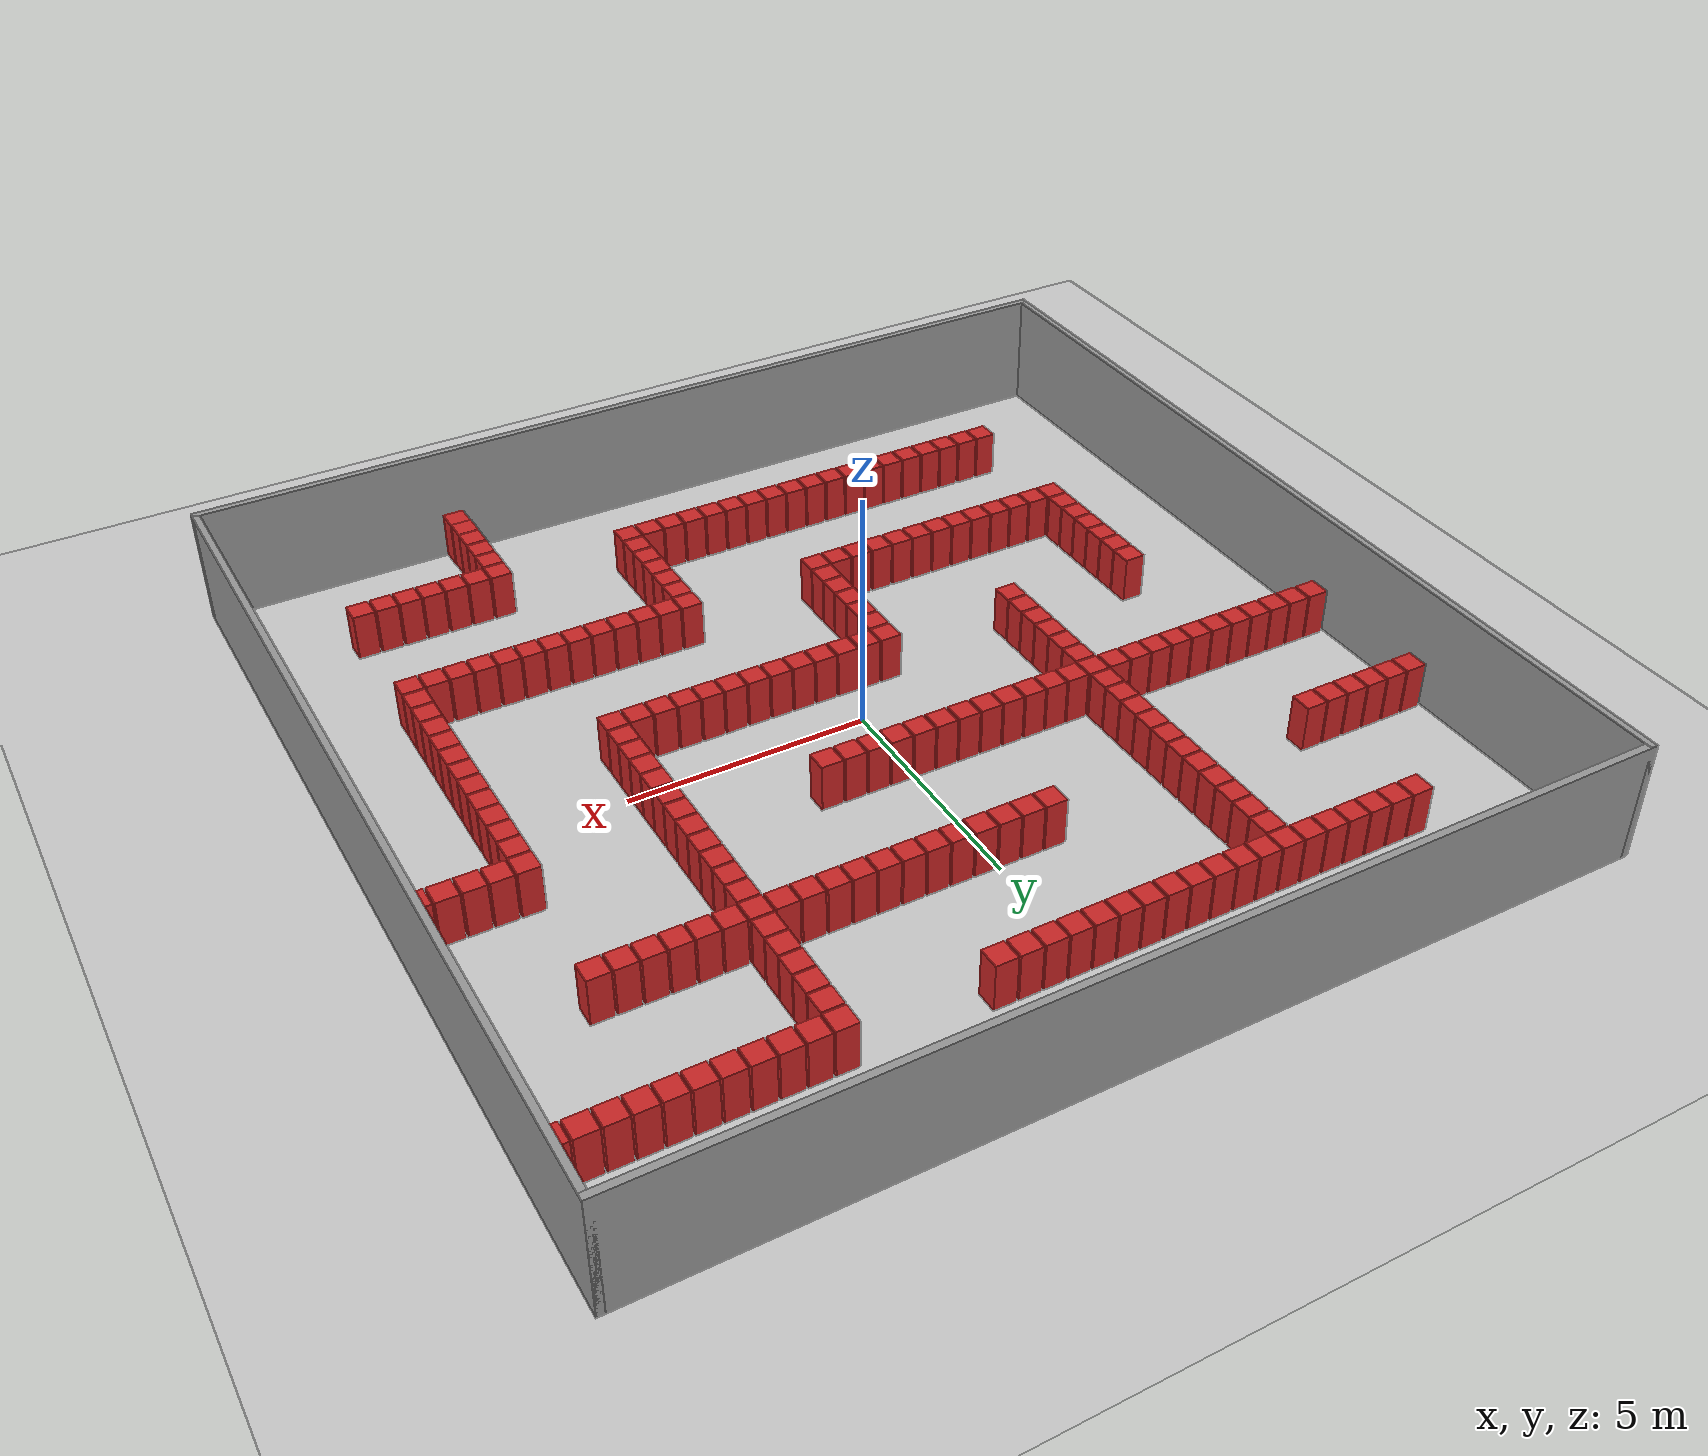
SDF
<sdf version="1.6">
 <world name="default">
  <light name="sun" type="directional">
   <pose>0 0 1000 0 -0 0</pose>
   <diffuse>0.8 0.8 0.8 1</diffuse>
   <specular>0.1 0.1 0.1 1</specular>
   <attenuation>
    <range>1000</range>
    <constant>0.9</constant>
    <linear>0.01</linear>
    <quadratic>0.001</quadratic>
   </attenuation>
   <direction>-0.5 0.5 -1</direction>
  </light>
  <model name="ground_plane">
   <static>1</static>
   <link name="link">
    <collision name="collision">
     <geometry><plane><normal>0 0 1</normal><size>100 100</size></plane></geometry>
     <surface><friction><ode><mu>100</mu><mu2>50</mu2></ode></friction></surface>
    </collision>
    <visual name="visual">
     <cast_shadows>0</cast_shadows>
     <geometry><plane><normal>0 0 1</normal><size>100 100</size></plane></geometry>
     <material>
      <script><uri>file://media/materials/scripts/gazebo.material</uri><name>Gazebo/Grey</name></script>
     </material>
    </visual>
   </link>
  </model>
  <gravity>0 0 -9.8</gravity>
  <magnetic_field>6e-06 2.3e-05 -4.2e-05</magnetic_field>
  <atmosphere type="adiabatic"/>
  <physics name="default_physics" default="0" type="ode">
   <max_step_size>0.001</max_step_size>
   <real_time_factor>1</real_time_factor>
   <real_time_update_rate>1000</real_time_update_rate>
  </physics>
  <scene><ambient>0.4 0.4 0.4 1</ambient><background>0.7 0.7 0.7 1</background><shadows>1</shadows></scene>
  <spherical_coordinates>
   <surface_model>EARTH_WGS84</surface_model>
   <latitude_deg>0</latitude_deg>
   <longitude_deg>0</longitude_deg>
   <elevation>0</elevation>
   <heading_deg>0</heading_deg>
  </spherical_coordinates>
  <model name="NamedLocations"><static>1</static><link name="DefaultStart"/></model>
  <model name="20x20_walls">
   <pose>0.044518 0.1761 0 0 -0 0</pose>
   <link name="Wall_1">
    <collision name="Wall_1_Collision">
     <geometry><box><size>20 0.15 2.5</size></box></geometry>
     <pose>0 0 1.25 0 -0 0</pose>
    </collision>
    <visual name="Wall_1_Visual">
     <pose>0 0 1.25 0 -0 0</pose>
     <geometry><box><size>20 0.15 2.5</size></box></geometry>
     <material>
      <script><uri>file://media/materials/scripts/gazebo.material</uri><name>Gazebo/Grey</name></script>
      <ambient>0.976471 0.992157 1 1</ambient>
     </material>
     <meta><layer>0</layer></meta>
    </visual>
    <pose>0 9.925 0 0 -0 0</pose>
   </link>
   <link name="Wall_3">
    <collision name="Wall_3_Collision">
     <geometry><box><size>20 0.15 2.5</size></box></geometry>
     <pose>0 0 1.25 0 -0 0</pose>
    </collision>
    <visual name="Wall_3_Visual">
     <pose>0 0 1.25 0 -0 0</pose>
     <geometry><box><size>20 0.15 2.5</size></box></geometry>
     <material>
      <script><uri>file://media/materials/scripts/gazebo.material</uri><name>Gazebo/Grey</name></script>
      <ambient>0.976471 0.992157 1 1</ambient>
     </material>
     <meta><layer>0</layer></meta>
    </visual>
    <pose>9.925 0 0 0 0 -1.5708</pose>
   </link>
   <link name="Wall_4">
    <collision name="Wall_4_Collision">
     <geometry><box><size>20 0.15 2.5</size></box></geometry>
     <pose>0 0 1.25 0 -0 0</pose>
    </collision>
    <visual name="Wall_4_Visual">
     <pose>0 0 1.25 0 -0 0</pose>
     <geometry><box><size>20 0.15 2.5</size></box></geometry>
     <material>
      <script><uri>file://media/materials/scripts/gazebo.material</uri><name>Gazebo/Grey</name></script>
      <ambient>0.976471 0.992157 1 1</ambient>
     </material>
     <meta><layer>0</layer></meta>
    </visual>
    <pose>0 -9.925 0 0 -0 3.14159</pose>
   </link>
   <link name="Wall_5">
    <collision name="Wall_5_Collision">
     <geometry><box><size>20 0.15 2.5</size></box></geometry>
     <pose>0 0 1.25 0 -0 0</pose>
    </collision>
    <visual name="Wall_5_Visual">
     <pose>0 0 1.25 0 -0 0</pose>
     <geometry><box><size>20 0.15 2.5</size></box></geometry>
     <material>
      <script><uri>file://media/materials/scripts/gazebo.material</uri><name>Gazebo/Grey</name></script>
      <ambient>0.976471 0.992157 1 1</ambient>
     </material>
     <meta><layer>0</layer></meta>
    </visual>
    <pose>-9.925 0 0 0 -0 1.5708</pose>
   </link>
   <static>1</static>
  </model>
  <model name="box_obstacle0">
   <static>0</static>
   <link name="link">
    <pose>0 0 0.1 0 -0 0</pose>
    <inertial>
     <mass>100</mass>
     <inertia>
      <ixx>0.166667</ixx>
      <ixy>0</ixy>
      <ixz>0</ixz>
      <iyy>0.166667</iyy>
      <iyz>0</iyz>
      <izz>0.166667</izz>
     </inertia>
    </inertial>
    <collision name="collision"><geometry><box><size>0.45 0.45 1</size></box></geometry></collision>
    <visual name="visual">
     <geometry><box><size>0.45 0.45 1</size></box></geometry>
     <material>
      <script><name>Gazebo/Red</name><uri>file://media/materials/scripts/gazebo.material</uri></script>
     </material>
    </visual>
   </link>
   <pose>-9.51051 1.75876 0.4 0 5e-06 0.002247</pose>
  </model>
  <model name="box_obstacle1">
   <static>0</static>
   <link name="link">
    <pose>0 0 0.1 0 -0 0</pose>
    <inertial>
     <mass>100</mass>
     <inertia>
      <ixx>0.166667</ixx>
      <ixy>0</ixy>
      <ixz>0</ixz>
      <iyy>0.166667</iyy>
      <iyz>0</iyz>
      <izz>0.166667</izz>
     </inertia>
    </inertial>
    <collision name="collision"><geometry><box><size>0.45 0.45 1</size></box></geometry></collision>
    <visual name="visual">
     <geometry><box><size>0.45 0.45 1</size></box></geometry>
     <material>
      <script><name>Gazebo/Red</name><uri>file://media/materials/scripts/gazebo.material</uri></script>
     </material>
    </visual>
   </link>
   <pose>-9.51051 4.69876 0.4 0 5e-06 0.002247</pose>
  </model>
  <model name="box_obstacle2">
   <static>0</static>
   <link name="link">
    <pose>0 0 0.1 0 -0 0</pose>
    <inertial>
     <mass>100</mass>
     <inertia>
      <ixx>0.166667</ixx>
      <ixy>0</ixy>
      <ixz>0</ixz>
      <iyy>0.166667</iyy>
      <iyz>0</iyz>
      <izz>0.166667</izz>
     </inertia>
    </inertial>
    <collision name="collision"><geometry><box><size>0.45 0.45 1</size></box></geometry></collision>
    <visual name="visual">
     <geometry><box><size>0.45 0.45 1</size></box></geometry>
     <material>
      <script><name>Gazebo/Red</name><uri>file://media/materials/scripts/gazebo.material</uri></script>
     </material>
    </visual>
   </link>
   <pose>-9.02051 1.75876 0.4 0 5e-06 0.002247</pose>
  </model>
  <model name="box_obstacle3">
   <static>0</static>
   <link name="link">
    <pose>0 0 0.1 0 -0 0</pose>
    <inertial>
     <mass>100</mass>
     <inertia>
      <ixx>0.166667</ixx>
      <ixy>0</ixy>
      <ixz>0</ixz>
      <iyy>0.166667</iyy>
      <iyz>0</iyz>
      <izz>0.166667</izz>
     </inertia>
    </inertial>
    <collision name="collision"><geometry><box><size>0.45 0.45 1</size></box></geometry></collision>
    <visual name="visual">
     <geometry><box><size>0.45 0.45 1</size></box></geometry>
     <material>
      <script><name>Gazebo/Red</name><uri>file://media/materials/scripts/gazebo.material</uri></script>
     </material>
    </visual>
   </link>
   <pose>-9.02051 4.69876 0.4 0 5e-06 0.002247</pose>
  </model>
  <model name="box_obstacle4">
   <static>0</static>
   <link name="link">
    <pose>0 0 0.1 0 -0 0</pose>
    <inertial>
     <mass>100</mass>
     <inertia>
      <ixx>0.166667</ixx>
      <ixy>0</ixy>
      <ixz>0</ixz>
      <iyy>0.166667</iyy>
      <iyz>0</iyz>
      <izz>0.166667</izz>
     </inertia>
    </inertial>
    <collision name="collision"><geometry><box><size>0.45 0.45 1</size></box></geometry></collision>
    <visual name="visual">
     <geometry><box><size>0.45 0.45 1</size></box></geometry>
     <material>
      <script><name>Gazebo/Red</name><uri>file://media/materials/scripts/gazebo.material</uri></script>
     </material>
    </visual>
   </link>
   <pose>-8.53051 1.75876 0.4 0 5e-06 0.002247</pose>
  </model>
  <model name="box_obstacle5">
   <static>0</static>
   <link name="link">
    <pose>0 0 0.1 0 -0 0</pose>
    <inertial>
     <mass>100</mass>
     <inertia>
      <ixx>0.166667</ixx>
      <ixy>0</ixy>
      <ixz>0</ixz>
      <iyy>0.166667</iyy>
      <iyz>0</iyz>
      <izz>0.166667</izz>
     </inertia>
    </inertial>
    <collision name="collision"><geometry><box><size>0.45 0.45 1</size></box></geometry></collision>
    <visual name="visual">
     <geometry><box><size>0.45 0.45 1</size></box></geometry>
     <material>
      <script><name>Gazebo/Red</name><uri>file://media/materials/scripts/gazebo.material</uri></script>
     </material>
    </visual>
   </link>
   <pose>-8.53051 4.69876 0.4 0 5e-06 0.002247</pose>
  </model>
  <model name="box_obstacle6">
   <static>0</static>
   <link name="link">
    <pose>0 0 0.1 0 -0 0</pose>
    <inertial>
     <mass>100</mass>
     <inertia>
      <ixx>0.166667</ixx>
      <ixy>0</ixy>
      <ixz>0</ixz>
      <iyy>0.166667</iyy>
      <iyz>0</iyz>
      <izz>0.166667</izz>
     </inertia>
    </inertial>
    <collision name="collision"><geometry><box><size>0.45 0.45 1</size></box></geometry></collision>
    <visual name="visual">
     <geometry><box><size>0.45 0.45 1</size></box></geometry>
     <material>
      <script><name>Gazebo/Red</name><uri>file://media/materials/scripts/gazebo.material</uri></script>
     </material>
    </visual>
   </link>
   <pose>-8.04051 1.75876 0.4 0 5e-06 0.002247</pose>
  </model>
  <model name="box_obstacle7">
   <static>0</static>
   <link name="link">
    <pose>0 0 0.1 0 -0 0</pose>
    <inertial>
     <mass>100</mass>
     <inertia>
      <ixx>0.166667</ixx>
      <ixy>0</ixy>
      <ixz>0</ixz>
      <iyy>0.166667</iyy>
      <iyz>0</iyz>
      <izz>0.166667</izz>
     </inertia>
    </inertial>
    <collision name="collision"><geometry><box><size>0.45 0.45 1</size></box></geometry></collision>
    <visual name="visual">
     <geometry><box><size>0.45 0.45 1</size></box></geometry>
     <material>
      <script><name>Gazebo/Red</name><uri>file://media/materials/scripts/gazebo.material</uri></script>
     </material>
    </visual>
   </link>
   <pose>-8.04051 4.69876 0.4 0 5e-06 0.002247</pose>
  </model>
  <model name="box_obstacle8">
   <static>0</static>
   <link name="link">
    <pose>0 0 0.1 0 -0 0</pose>
    <inertial>
     <mass>100</mass>
     <inertia>
      <ixx>0.166667</ixx>
      <ixy>0</ixy>
      <ixz>0</ixz>
      <iyy>0.166667</iyy>
      <iyz>0</iyz>
      <izz>0.166667</izz>
     </inertia>
    </inertial>
    <collision name="collision"><geometry><box><size>0.45 0.45 1</size></box></geometry></collision>
    <visual name="visual">
     <geometry><box><size>0.45 0.45 1</size></box></geometry>
     <material>
      <script><name>Gazebo/Red</name><uri>file://media/materials/scripts/gazebo.material</uri></script>
     </material>
    </visual>
   </link>
   <pose>-7.55051 1.75876 0.4 0 5e-06 0.002247</pose>
  </model>
  <model name="box_obstacle9">
   <static>0</static>
   <link name="link">
    <pose>0 0 0.1 0 -0 0</pose>
    <inertial>
     <mass>100</mass>
     <inertia>
      <ixx>0.166667</ixx>
      <ixy>0</ixy>
      <ixz>0</ixz>
      <iyy>0.166667</iyy>
      <iyz>0</iyz>
      <izz>0.166667</izz>
     </inertia>
    </inertial>
    <collision name="collision"><geometry><box><size>0.45 0.45 1</size></box></geometry></collision>
    <visual name="visual">
     <geometry><box><size>0.45 0.45 1</size></box></geometry>
     <material>
      <script><name>Gazebo/Red</name><uri>file://media/materials/scripts/gazebo.material</uri></script>
     </material>
    </visual>
   </link>
   <pose>-7.55051 4.69876 0.4 0 5e-06 0.002247</pose>
  </model>
  <model name="box_obstacle10">
   <static>0</static>
   <link name="link">
    <pose>0 0 0.1 0 -0 0</pose>
    <inertial>
     <mass>100</mass>
     <inertia>
      <ixx>0.166667</ixx>
      <ixy>0</ixy>
      <ixz>0</ixz>
      <iyy>0.166667</iyy>
      <iyz>0</iyz>
      <izz>0.166667</izz>
     </inertia>
    </inertial>
    <collision name="collision"><geometry><box><size>0.45 0.45 1</size></box></geometry></collision>
    <visual name="visual">
     <geometry><box><size>0.45 0.45 1</size></box></geometry>
     <material>
      <script><name>Gazebo/Red</name><uri>file://media/materials/scripts/gazebo.material</uri></script>
     </material>
    </visual>
   </link>
   <pose>-7.06051 -7.06124 0.4 0 5e-06 0.002247</pose>
  </model>
  <model name="box_obstacle11">
   <static>0</static>
   <link name="link">
    <pose>0 0 0.1 0 -0 0</pose>
    <inertial>
     <mass>100</mass>
     <inertia>
      <ixx>0.166667</ixx>
      <ixy>0</ixy>
      <ixz>0</ixz>
      <iyy>0.166667</iyy>
      <iyz>0</iyz>
      <izz>0.166667</izz>
     </inertia>
    </inertial>
    <collision name="collision"><geometry><box><size>0.45 0.45 1</size></box></geometry></collision>
    <visual name="visual">
     <geometry><box><size>0.45 0.45 1</size></box></geometry>
     <material>
      <script><name>Gazebo/Red</name><uri>file://media/materials/scripts/gazebo.material</uri></script>
     </material>
    </visual>
   </link>
   <pose>-7.06051 -4.12124 0.4 0 5e-06 0.002247</pose>
  </model>
  <model name="box_obstacle12">
   <static>0</static>
   <link name="link">
    <pose>0 0 0.1 0 -0 0</pose>
    <inertial>
     <mass>100</mass>
     <inertia>
      <ixx>0.166667</ixx>
      <ixy>0</ixy>
      <ixz>0</ixz>
      <iyy>0.166667</iyy>
      <iyz>0</iyz>
      <izz>0.166667</izz>
     </inertia>
    </inertial>
    <collision name="collision"><geometry><box><size>0.45 0.45 1</size></box></geometry></collision>
    <visual name="visual">
     <geometry><box><size>0.45 0.45 1</size></box></geometry>
     <material>
      <script><name>Gazebo/Red</name><uri>file://media/materials/scripts/gazebo.material</uri></script>
     </material>
    </visual>
   </link>
   <pose>-7.06051 -3.63124 0.4 0 5e-06 0.002247</pose>
  </model>
  <model name="box_obstacle13">
   <static>0</static>
   <link name="link">
    <pose>0 0 0.1 0 -0 0</pose>
    <inertial>
     <mass>100</mass>
     <inertia>
      <ixx>0.166667</ixx>
      <ixy>0</ixy>
      <ixz>0</ixz>
      <iyy>0.166667</iyy>
      <iyz>0</iyz>
      <izz>0.166667</izz>
     </inertia>
    </inertial>
    <collision name="collision"><geometry><box><size>0.45 0.45 1</size></box></geometry></collision>
    <visual name="visual">
     <geometry><box><size>0.45 0.45 1</size></box></geometry>
     <material>
      <script><name>Gazebo/Red</name><uri>file://media/materials/scripts/gazebo.material</uri></script>
     </material>
    </visual>
   </link>
   <pose>-7.06051 -3.14124 0.4 0 5e-06 0.002247</pose>
  </model>
  <model name="box_obstacle14">
   <static>0</static>
   <link name="link">
    <pose>0 0 0.1 0 -0 0</pose>
    <inertial>
     <mass>100</mass>
     <inertia>
      <ixx>0.166667</ixx>
      <ixy>0</ixy>
      <ixz>0</ixz>
      <iyy>0.166667</iyy>
      <iyz>0</iyz>
      <izz>0.166667</izz>
     </inertia>
    </inertial>
    <collision name="collision"><geometry><box><size>0.45 0.45 1</size></box></geometry></collision>
    <visual name="visual">
     <geometry><box><size>0.45 0.45 1</size></box></geometry>
     <material>
      <script><name>Gazebo/Red</name><uri>file://media/materials/scripts/gazebo.material</uri></script>
     </material>
    </visual>
   </link>
   <pose>-7.06051 -2.65124 0.4 0 5e-06 0.002247</pose>
  </model>
  <model name="box_obstacle15">
   <static>0</static>
   <link name="link">
    <pose>0 0 0.1 0 -0 0</pose>
    <inertial>
     <mass>100</mass>
     <inertia>
      <ixx>0.166667</ixx>
      <ixy>0</ixy>
      <ixz>0</ixz>
      <iyy>0.166667</iyy>
      <iyz>0</iyz>
      <izz>0.166667</izz>
     </inertia>
    </inertial>
    <collision name="collision"><geometry><box><size>0.45 0.45 1</size></box></geometry></collision>
    <visual name="visual">
     <geometry><box><size>0.45 0.45 1</size></box></geometry>
     <material>
      <script><name>Gazebo/Red</name><uri>file://media/materials/scripts/gazebo.material</uri></script>
     </material>
    </visual>
   </link>
   <pose>-7.06051 -2.16124 0.4 0 5e-06 0.002247</pose>
  </model>
  <model name="box_obstacle16">
   <static>0</static>
   <link name="link">
    <pose>0 0 0.1 0 -0 0</pose>
    <inertial>
     <mass>100</mass>
     <inertia>
      <ixx>0.166667</ixx>
      <ixy>0</ixy>
      <ixz>0</ixz>
      <iyy>0.166667</iyy>
      <iyz>0</iyz>
      <izz>0.166667</izz>
     </inertia>
    </inertial>
    <collision name="collision"><geometry><box><size>0.45 0.45 1</size></box></geometry></collision>
    <visual name="visual">
     <geometry><box><size>0.45 0.45 1</size></box></geometry>
     <material>
      <script><name>Gazebo/Red</name><uri>file://media/materials/scripts/gazebo.material</uri></script>
     </material>
    </visual>
   </link>
   <pose>-7.06051 -1.67124 0.4 0 5e-06 0.002247</pose>
  </model>
  <model name="box_obstacle17">
   <static>0</static>
   <link name="link">
    <pose>0 0 0.1 0 -0 0</pose>
    <inertial>
     <mass>100</mass>
     <inertia>
      <ixx>0.166667</ixx>
      <ixy>0</ixy>
      <ixz>0</ixz>
      <iyy>0.166667</iyy>
      <iyz>0</iyz>
      <izz>0.166667</izz>
     </inertia>
    </inertial>
    <collision name="collision"><geometry><box><size>0.45 0.45 1</size></box></geometry></collision>
    <visual name="visual">
     <geometry><box><size>0.45 0.45 1</size></box></geometry>
     <material>
      <script><name>Gazebo/Red</name><uri>file://media/materials/scripts/gazebo.material</uri></script>
     </material>
    </visual>
   </link>
   <pose>-7.06051 -1.18124 0.4 0 5e-06 0.002247</pose>
  </model>
  <model name="box_obstacle18">
   <static>0</static>
   <link name="link">
    <pose>0 0 0.1 0 -0 0</pose>
    <inertial>
     <mass>100</mass>
     <inertia>
      <ixx>0.166667</ixx>
      <ixy>0</ixy>
      <ixz>0</ixz>
      <iyy>0.166667</iyy>
      <iyz>0</iyz>
      <izz>0.166667</izz>
     </inertia>
    </inertial>
    <collision name="collision"><geometry><box><size>0.45 0.45 1</size></box></geometry></collision>
    <visual name="visual">
     <geometry><box><size>0.45 0.45 1</size></box></geometry>
     <material>
      <script><name>Gazebo/Red</name><uri>file://media/materials/scripts/gazebo.material</uri></script>
     </material>
    </visual>
   </link>
   <pose>-7.06051 1.75876 0.4 0 5e-06 0.002247</pose>
  </model>
  <model name="box_obstacle19">
   <static>0</static>
   <link name="link">
    <pose>0 0 0.1 0 -0 0</pose>
    <inertial>
     <mass>100</mass>
     <inertia>
      <ixx>0.166667</ixx>
      <ixy>0</ixy>
      <ixz>0</ixz>
      <iyy>0.166667</iyy>
      <iyz>0</iyz>
      <izz>0.166667</izz>
     </inertia>
    </inertial>
    <collision name="collision"><geometry><box><size>0.45 0.45 1</size></box></geometry></collision>
    <visual name="visual">
     <geometry><box><size>0.45 0.45 1</size></box></geometry>
     <material>
      <script><name>Gazebo/Red</name><uri>file://media/materials/scripts/gazebo.material</uri></script>
     </material>
    </visual>
   </link>
   <pose>-7.06051 4.69876 0.4 0 5e-06 0.002247</pose>
  </model>
  <model name="box_obstacle20">
   <static>0</static>
   <link name="link">
    <pose>0 0 0.1 0 -0 0</pose>
    <inertial>
     <mass>100</mass>
     <inertia>
      <ixx>0.166667</ixx>
      <ixy>0</ixy>
      <ixz>0</ixz>
      <iyy>0.166667</iyy>
      <iyz>0</iyz>
      <izz>0.166667</izz>
     </inertia>
    </inertial>
    <collision name="collision"><geometry><box><size>0.45 0.45 1</size></box></geometry></collision>
    <visual name="visual">
     <geometry><box><size>0.45 0.45 1</size></box></geometry>
     <material>
      <script><name>Gazebo/Red</name><uri>file://media/materials/scripts/gazebo.material</uri></script>
     </material>
    </visual>
   </link>
   <pose>-7.06051 7.63876 0.4 0 5e-06 0.002247</pose>
  </model>
  <model name="box_obstacle21">
   <static>0</static>
   <link name="link">
    <pose>0 0 0.1 0 -0 0</pose>
    <inertial>
     <mass>100</mass>
     <inertia>
      <ixx>0.166667</ixx>
      <ixy>0</ixy>
      <ixz>0</ixz>
      <iyy>0.166667</iyy>
      <iyz>0</iyz>
      <izz>0.166667</izz>
     </inertia>
    </inertial>
    <collision name="collision"><geometry><box><size>0.45 0.45 1</size></box></geometry></collision>
    <visual name="visual">
     <geometry><box><size>0.45 0.45 1</size></box></geometry>
     <material>
      <script><name>Gazebo/Red</name><uri>file://media/materials/scripts/gazebo.material</uri></script>
     </material>
    </visual>
   </link>
   <pose>-6.57051 -7.06124 0.4 0 5e-06 0.002247</pose>
  </model>
  <model name="box_obstacle22">
   <static>0</static>
   <link name="link">
    <pose>0 0 0.1 0 -0 0</pose>
    <inertial>
     <mass>100</mass>
     <inertia>
      <ixx>0.166667</ixx>
      <ixy>0</ixy>
      <ixz>0</ixz>
      <iyy>0.166667</iyy>
      <iyz>0</iyz>
      <izz>0.166667</izz>
     </inertia>
    </inertial>
    <collision name="collision"><geometry><box><size>0.45 0.45 1</size></box></geometry></collision>
    <visual name="visual">
     <geometry><box><size>0.45 0.45 1</size></box></geometry>
     <material>
      <script><name>Gazebo/Red</name><uri>file://media/materials/scripts/gazebo.material</uri></script>
     </material>
    </visual>
   </link>
   <pose>-6.57051 -4.12124 0.4 0 5e-06 0.002247</pose>
  </model>
  <model name="box_obstacle23">
   <static>0</static>
   <link name="link">
    <pose>0 0 0.1 0 -0 0</pose>
    <inertial>
     <mass>100</mass>
     <inertia>
      <ixx>0.166667</ixx>
      <ixy>0</ixy>
      <ixz>0</ixz>
      <iyy>0.166667</iyy>
      <iyz>0</iyz>
      <izz>0.166667</izz>
     </inertia>
    </inertial>
    <collision name="collision"><geometry><box><size>0.45 0.45 1</size></box></geometry></collision>
    <visual name="visual">
     <geometry><box><size>0.45 0.45 1</size></box></geometry>
     <material>
      <script><name>Gazebo/Red</name><uri>file://media/materials/scripts/gazebo.material</uri></script>
     </material>
    </visual>
   </link>
   <pose>-6.57051 1.75876 0.4 0 5e-06 0.002247</pose>
  </model>
  <model name="box_obstacle24">
   <static>0</static>
   <link name="link">
    <pose>0 0 0.1 0 -0 0</pose>
    <inertial>
     <mass>100</mass>
     <inertia>
      <ixx>0.166667</ixx>
      <ixy>0</ixy>
      <ixz>0</ixz>
      <iyy>0.166667</iyy>
      <iyz>0</iyz>
      <izz>0.166667</izz>
     </inertia>
    </inertial>
    <collision name="collision"><geometry><box><size>0.45 0.45 1</size></box></geometry></collision>
    <visual name="visual">
     <geometry><box><size>0.45 0.45 1</size></box></geometry>
     <material>
      <script><name>Gazebo/Red</name><uri>file://media/materials/scripts/gazebo.material</uri></script>
     </material>
    </visual>
   </link>
   <pose>-6.57051 7.63876 0.4 0 5e-06 0.002247</pose>
  </model>
  <model name="box_obstacle25">
   <static>0</static>
   <link name="link">
    <pose>0 0 0.1 0 -0 0</pose>
    <inertial>
     <mass>100</mass>
     <inertia>
      <ixx>0.166667</ixx>
      <ixy>0</ixy>
      <ixz>0</ixz>
      <iyy>0.166667</iyy>
      <iyz>0</iyz>
      <izz>0.166667</izz>
     </inertia>
    </inertial>
    <collision name="collision"><geometry><box><size>0.45 0.45 1</size></box></geometry></collision>
    <visual name="visual">
     <geometry><box><size>0.45 0.45 1</size></box></geometry>
     <material>
      <script><name>Gazebo/Red</name><uri>file://media/materials/scripts/gazebo.material</uri></script>
     </material>
    </visual>
   </link>
   <pose>-6.08051 -7.06124 0.4 0 5e-06 0.002247</pose>
  </model>
  <model name="box_obstacle26">
   <static>0</static>
   <link name="link">
    <pose>0 0 0.1 0 -0 0</pose>
    <inertial>
     <mass>100</mass>
     <inertia>
      <ixx>0.166667</ixx>
      <ixy>0</ixy>
      <ixz>0</ixz>
      <iyy>0.166667</iyy>
      <iyz>0</iyz>
      <izz>0.166667</izz>
     </inertia>
    </inertial>
    <collision name="collision"><geometry><box><size>0.45 0.45 1</size></box></geometry></collision>
    <visual name="visual">
     <geometry><box><size>0.45 0.45 1</size></box></geometry>
     <material>
      <script><name>Gazebo/Red</name><uri>file://media/materials/scripts/gazebo.material</uri></script>
     </material>
    </visual>
   </link>
   <pose>-6.08051 -4.12124 0.4 0 5e-06 0.002247</pose>
  </model>
  <model name="box_obstacle27">
   <static>0</static>
   <link name="link">
    <pose>0 0 0.1 0 -0 0</pose>
    <inertial>
     <mass>100</mass>
     <inertia>
      <ixx>0.166667</ixx>
      <ixy>0</ixy>
      <ixz>0</ixz>
      <iyy>0.166667</iyy>
      <iyz>0</iyz>
      <izz>0.166667</izz>
     </inertia>
    </inertial>
    <collision name="collision"><geometry><box><size>0.45 0.45 1</size></box></geometry></collision>
    <visual name="visual">
     <geometry><box><size>0.45 0.45 1</size></box></geometry>
     <material>
      <script><name>Gazebo/Red</name><uri>file://media/materials/scripts/gazebo.material</uri></script>
     </material>
    </visual>
   </link>
   <pose>-6.08051 1.75876 0.4 0 5e-06 0.002247</pose>
  </model>
  <model name="box_obstacle28">
   <static>0</static>
   <link name="link">
    <pose>0 0 0.1 0 -0 0</pose>
    <inertial>
     <mass>100</mass>
     <inertia>
      <ixx>0.166667</ixx>
      <ixy>0</ixy>
      <ixz>0</ixz>
      <iyy>0.166667</iyy>
      <iyz>0</iyz>
      <izz>0.166667</izz>
     </inertia>
    </inertial>
    <collision name="collision"><geometry><box><size>0.45 0.45 1</size></box></geometry></collision>
    <visual name="visual">
     <geometry><box><size>0.45 0.45 1</size></box></geometry>
     <material>
      <script><name>Gazebo/Red</name><uri>file://media/materials/scripts/gazebo.material</uri></script>
     </material>
    </visual>
   </link>
   <pose>-6.08051 7.63876 0.4 0 5e-06 0.002247</pose>
  </model>
  <model name="box_obstacle29">
   <static>0</static>
   <link name="link">
    <pose>0 0 0.1 0 -0 0</pose>
    <inertial>
     <mass>100</mass>
     <inertia>
      <ixx>0.166667</ixx>
      <ixy>0</ixy>
      <ixz>0</ixz>
      <iyy>0.166667</iyy>
      <iyz>0</iyz>
      <izz>0.166667</izz>
     </inertia>
    </inertial>
    <collision name="collision"><geometry><box><size>0.45 0.45 1</size></box></geometry></collision>
    <visual name="visual">
     <geometry><box><size>0.45 0.45 1</size></box></geometry>
     <material>
      <script><name>Gazebo/Red</name><uri>file://media/materials/scripts/gazebo.material</uri></script>
     </material>
    </visual>
   </link>
   <pose>-5.59051 -7.06124 0.4 0 5e-06 0.002247</pose>
  </model>
  <model name="box_obstacle30">
   <static>0</static>
   <link name="link">
    <pose>0 0 0.1 0 -0 0</pose>
    <inertial>
     <mass>100</mass>
     <inertia>
      <ixx>0.166667</ixx>
      <ixy>0</ixy>
      <ixz>0</ixz>
      <iyy>0.166667</iyy>
      <iyz>0</iyz>
      <izz>0.166667</izz>
     </inertia>
    </inertial>
    <collision name="collision"><geometry><box><size>0.45 0.45 1</size></box></geometry></collision>
    <visual name="visual">
     <geometry><box><size>0.45 0.45 1</size></box></geometry>
     <material>
      <script><name>Gazebo/Red</name><uri>file://media/materials/scripts/gazebo.material</uri></script>
     </material>
    </visual>
   </link>
   <pose>-5.59051 -4.12124 0.4 0 5e-06 0.002247</pose>
  </model>
  <model name="box_obstacle31">
   <static>0</static>
   <link name="link">
    <pose>0 0 0.1 0 -0 0</pose>
    <inertial>
     <mass>100</mass>
     <inertia>
      <ixx>0.166667</ixx>
      <ixy>0</ixy>
      <ixz>0</ixz>
      <iyy>0.166667</iyy>
      <iyz>0</iyz>
      <izz>0.166667</izz>
     </inertia>
    </inertial>
    <collision name="collision"><geometry><box><size>0.45 0.45 1</size></box></geometry></collision>
    <visual name="visual">
     <geometry><box><size>0.45 0.45 1</size></box></geometry>
     <material>
      <script><name>Gazebo/Red</name><uri>file://media/materials/scripts/gazebo.material</uri></script>
     </material>
    </visual>
   </link>
   <pose>-5.59051 1.75876 0.4 0 5e-06 0.002247</pose>
  </model>
  <model name="box_obstacle32">
   <static>0</static>
   <link name="link">
    <pose>0 0 0.1 0 -0 0</pose>
    <inertial>
     <mass>100</mass>
     <inertia>
      <ixx>0.166667</ixx>
      <ixy>0</ixy>
      <ixz>0</ixz>
      <iyy>0.166667</iyy>
      <iyz>0</iyz>
      <izz>0.166667</izz>
     </inertia>
    </inertial>
    <collision name="collision"><geometry><box><size>0.45 0.45 1</size></box></geometry></collision>
    <visual name="visual">
     <geometry><box><size>0.45 0.45 1</size></box></geometry>
     <material>
      <script><name>Gazebo/Red</name><uri>file://media/materials/scripts/gazebo.material</uri></script>
     </material>
    </visual>
   </link>
   <pose>-5.59051 7.63876 0.4 0 5e-06 0.002247</pose>
  </model>
  <model name="box_obstacle33">
   <static>0</static>
   <link name="link">
    <pose>0 0 0.1 0 -0 0</pose>
    <inertial>
     <mass>100</mass>
     <inertia>
      <ixx>0.166667</ixx>
      <ixy>0</ixy>
      <ixz>0</ixz>
      <iyy>0.166667</iyy>
      <iyz>0</iyz>
      <izz>0.166667</izz>
     </inertia>
    </inertial>
    <collision name="collision"><geometry><box><size>0.45 0.45 1</size></box></geometry></collision>
    <visual name="visual">
     <geometry><box><size>0.45 0.45 1</size></box></geometry>
     <material>
      <script><name>Gazebo/Red</name><uri>file://media/materials/scripts/gazebo.material</uri></script>
     </material>
    </visual>
   </link>
   <pose>-5.10051 -7.06124 0.4 0 5e-06 0.002247</pose>
  </model>
  <model name="box_obstacle34">
   <static>0</static>
   <link name="link">
    <pose>0 0 0.1 0 -0 0</pose>
    <inertial>
     <mass>100</mass>
     <inertia>
      <ixx>0.166667</ixx>
      <ixy>0</ixy>
      <ixz>0</ixz>
      <iyy>0.166667</iyy>
      <iyz>0</iyz>
      <izz>0.166667</izz>
     </inertia>
    </inertial>
    <collision name="collision"><geometry><box><size>0.45 0.45 1</size></box></geometry></collision>
    <visual name="visual">
     <geometry><box><size>0.45 0.45 1</size></box></geometry>
     <material>
      <script><name>Gazebo/Red</name><uri>file://media/materials/scripts/gazebo.material</uri></script>
     </material>
    </visual>
   </link>
   <pose>-5.10051 -4.12124 0.4 0 5e-06 0.002247</pose>
  </model>
  <model name="box_obstacle35">
   <static>0</static>
   <link name="link">
    <pose>0 0 0.1 0 -0 0</pose>
    <inertial>
     <mass>100</mass>
     <inertia>
      <ixx>0.166667</ixx>
      <ixy>0</ixy>
      <ixz>0</ixz>
      <iyy>0.166667</iyy>
      <iyz>0</iyz>
      <izz>0.166667</izz>
     </inertia>
    </inertial>
    <collision name="collision"><geometry><box><size>0.45 0.45 1</size></box></geometry></collision>
    <visual name="visual">
     <geometry><box><size>0.45 0.45 1</size></box></geometry>
     <material>
      <script><name>Gazebo/Red</name><uri>file://media/materials/scripts/gazebo.material</uri></script>
     </material>
    </visual>
   </link>
   <pose>-5.10051 1.75876 0.4 0 5e-06 0.002247</pose>
  </model>
  <model name="box_obstacle36">
   <static>0</static>
   <link name="link">
    <pose>0 0 0.1 0 -0 0</pose>
    <inertial>
     <mass>100</mass>
     <inertia>
      <ixx>0.166667</ixx>
      <ixy>0</ixy>
      <ixz>0</ixz>
      <iyy>0.166667</iyy>
      <iyz>0</iyz>
      <izz>0.166667</izz>
     </inertia>
    </inertial>
    <collision name="collision"><geometry><box><size>0.45 0.45 1</size></box></geometry></collision>
    <visual name="visual">
     <geometry><box><size>0.45 0.45 1</size></box></geometry>
     <material>
      <script><name>Gazebo/Red</name><uri>file://media/materials/scripts/gazebo.material</uri></script>
     </material>
    </visual>
   </link>
   <pose>-5.10051 7.63876 0.4 0 5e-06 0.002247</pose>
  </model>
  <model name="box_obstacle37">
   <static>0</static>
   <link name="link">
    <pose>0 0 0.1 0 -0 0</pose>
    <inertial>
     <mass>100</mass>
     <inertia>
      <ixx>0.166667</ixx>
      <ixy>0</ixy>
      <ixz>0</ixz>
      <iyy>0.166667</iyy>
      <iyz>0</iyz>
      <izz>0.166667</izz>
     </inertia>
    </inertial>
    <collision name="collision"><geometry><box><size>0.45 0.45 1</size></box></geometry></collision>
    <visual name="visual">
     <geometry><box><size>0.45 0.45 1</size></box></geometry>
     <material>
      <script><name>Gazebo/Red</name><uri>file://media/materials/scripts/gazebo.material</uri></script>
     </material>
    </visual>
   </link>
   <pose>-4.61051 -7.06124 0.4 0 5e-06 0.002247</pose>
  </model>
  <model name="box_obstacle38">
   <static>0</static>
   <link name="link">
    <pose>0 0 0.1 0 -0 0</pose>
    <inertial>
     <mass>100</mass>
     <inertia>
      <ixx>0.166667</ixx>
      <ixy>0</ixy>
      <ixz>0</ixz>
      <iyy>0.166667</iyy>
      <iyz>0</iyz>
      <izz>0.166667</izz>
     </inertia>
    </inertial>
    <collision name="collision"><geometry><box><size>0.45 0.45 1</size></box></geometry></collision>
    <visual name="visual">
     <geometry><box><size>0.45 0.45 1</size></box></geometry>
     <material>
      <script><name>Gazebo/Red</name><uri>file://media/materials/scripts/gazebo.material</uri></script>
     </material>
    </visual>
   </link>
   <pose>-4.61051 -4.12124 0.4 0 5e-06 0.002247</pose>
  </model>
  <model name="box_obstacle39">
   <static>0</static>
   <link name="link">
    <pose>0 0 0.1 0 -0 0</pose>
    <inertial>
     <mass>100</mass>
     <inertia>
      <ixx>0.166667</ixx>
      <ixy>0</ixy>
      <ixz>0</ixz>
      <iyy>0.166667</iyy>
      <iyz>0</iyz>
      <izz>0.166667</izz>
     </inertia>
    </inertial>
    <collision name="collision"><geometry><box><size>0.45 0.45 1</size></box></geometry></collision>
    <visual name="visual">
     <geometry><box><size>0.45 0.45 1</size></box></geometry>
     <material>
      <script><name>Gazebo/Red</name><uri>file://media/materials/scripts/gazebo.material</uri></script>
     </material>
    </visual>
   </link>
   <pose>-4.61051 1.75876 0.4 0 5e-06 0.002247</pose>
  </model>
  <model name="box_obstacle40">
   <static>0</static>
   <link name="link">
    <pose>0 0 0.1 0 -0 0</pose>
    <inertial>
     <mass>100</mass>
     <inertia>
      <ixx>0.166667</ixx>
      <ixy>0</ixy>
      <ixz>0</ixz>
      <iyy>0.166667</iyy>
      <iyz>0</iyz>
      <izz>0.166667</izz>
     </inertia>
    </inertial>
    <collision name="collision"><geometry><box><size>0.45 0.45 1</size></box></geometry></collision>
    <visual name="visual">
     <geometry><box><size>0.45 0.45 1</size></box></geometry>
     <material>
      <script><name>Gazebo/Red</name><uri>file://media/materials/scripts/gazebo.material</uri></script>
     </material>
    </visual>
   </link>
   <pose>-4.61051 7.63876 0.4 0 5e-06 0.002247</pose>
  </model>
  <model name="box_obstacle41">
   <static>0</static>
   <link name="link">
    <pose>0 0 0.1 0 -0 0</pose>
    <inertial>
     <mass>100</mass>
     <inertia>
      <ixx>0.166667</ixx>
      <ixy>0</ixy>
      <ixz>0</ixz>
      <iyy>0.166667</iyy>
      <iyz>0</iyz>
      <izz>0.166667</izz>
     </inertia>
    </inertial>
    <collision name="collision"><geometry><box><size>0.45 0.45 1</size></box></geometry></collision>
    <visual name="visual">
     <geometry><box><size>0.45 0.45 1</size></box></geometry>
     <material>
      <script><name>Gazebo/Red</name><uri>file://media/materials/scripts/gazebo.material</uri></script>
     </material>
    </visual>
   </link>
   <pose>-4.12051 -7.06124 0.4 0 5e-06 0.002247</pose>
  </model>
  <model name="box_obstacle42">
   <static>0</static>
   <link name="link">
    <pose>0 0 0.1 0 -0 0</pose>
    <inertial>
     <mass>100</mass>
     <inertia>
      <ixx>0.166667</ixx>
      <ixy>0</ixy>
      <ixz>0</ixz>
      <iyy>0.166667</iyy>
      <iyz>0</iyz>
      <izz>0.166667</izz>
     </inertia>
    </inertial>
    <collision name="collision"><geometry><box><size>0.45 0.45 1</size></box></geometry></collision>
    <visual name="visual">
     <geometry><box><size>0.45 0.45 1</size></box></geometry>
     <material>
      <script><name>Gazebo/Red</name><uri>file://media/materials/scripts/gazebo.material</uri></script>
     </material>
    </visual>
   </link>
   <pose>-4.12051 -4.12124 0.4 0 5e-06 0.002247</pose>
  </model>
  <model name="box_obstacle43">
   <static>0</static>
   <link name="link">
    <pose>0 0 0.1 0 -0 0</pose>
    <inertial>
     <mass>100</mass>
     <inertia>
      <ixx>0.166667</ixx>
      <ixy>0</ixy>
      <ixz>0</ixz>
      <iyy>0.166667</iyy>
      <iyz>0</iyz>
      <izz>0.166667</izz>
     </inertia>
    </inertial>
    <collision name="collision"><geometry><box><size>0.45 0.45 1</size></box></geometry></collision>
    <visual name="visual">
     <geometry><box><size>0.45 0.45 1</size></box></geometry>
     <material>
      <script><name>Gazebo/Red</name><uri>file://media/materials/scripts/gazebo.material</uri></script>
     </material>
    </visual>
   </link>
   <pose>-4.12051 -1.18124 0.4 0 5e-06 0.002247</pose>
  </model>
  <model name="box_obstacle44">
   <static>0</static>
   <link name="link">
    <pose>0 0 0.1 0 -0 0</pose>
    <inertial>
     <mass>100</mass>
     <inertia>
      <ixx>0.166667</ixx>
      <ixy>0</ixy>
      <ixz>0</ixz>
      <iyy>0.166667</iyy>
      <iyz>0</iyz>
      <izz>0.166667</izz>
     </inertia>
    </inertial>
    <collision name="collision"><geometry><box><size>0.45 0.45 1</size></box></geometry></collision>
    <visual name="visual">
     <geometry><box><size>0.45 0.45 1</size></box></geometry>
     <material>
      <script><name>Gazebo/Red</name><uri>file://media/materials/scripts/gazebo.material</uri></script>
     </material>
    </visual>
   </link>
   <pose>-4.12051 -0.691242 0.4 0 5e-06 0.002247</pose>
  </model>
  <model name="box_obstacle45">
   <static>0</static>
   <link name="link">
    <pose>0 0 0.1 0 -0 0</pose>
    <inertial>
     <mass>100</mass>
     <inertia>
      <ixx>0.166667</ixx>
      <ixy>0</ixy>
      <ixz>0</ixz>
      <iyy>0.166667</iyy>
      <iyz>0</iyz>
      <izz>0.166667</izz>
     </inertia>
    </inertial>
    <collision name="collision"><geometry><box><size>0.45 0.45 1</size></box></geometry></collision>
    <visual name="visual">
     <geometry><box><size>0.45 0.45 1</size></box></geometry>
     <material>
      <script><name>Gazebo/Red</name><uri>file://media/materials/scripts/gazebo.material</uri></script>
     </material>
    </visual>
   </link>
   <pose>-4.12051 -0.201242 0.4 0 5e-06 0.002247</pose>
  </model>
  <model name="box_obstacle46">
   <static>0</static>
   <link name="link">
    <pose>0 0 0.1 0 -0 0</pose>
    <inertial>
     <mass>100</mass>
     <inertia>
      <ixx>0.166667</ixx>
      <ixy>0</ixy>
      <ixz>0</ixz>
      <iyy>0.166667</iyy>
      <iyz>0</iyz>
      <izz>0.166667</izz>
     </inertia>
    </inertial>
    <collision name="collision"><geometry><box><size>0.45 0.45 1</size></box></geometry></collision>
    <visual name="visual">
     <geometry><box><size>0.45 0.45 1</size></box></geometry>
     <material>
      <script><name>Gazebo/Red</name><uri>file://media/materials/scripts/gazebo.material</uri></script>
     </material>
    </visual>
   </link>
   <pose>-4.12051 0.288758 0.4 0 5e-06 0.002247</pose>
  </model>
  <model name="box_obstacle47">
   <static>0</static>
   <link name="link">
    <pose>0 0 0.1 0 -0 0</pose>
    <inertial>
     <mass>100</mass>
     <inertia>
      <ixx>0.166667</ixx>
      <ixy>0</ixy>
      <ixz>0</ixz>
      <iyy>0.166667</iyy>
      <iyz>0</iyz>
      <izz>0.166667</izz>
     </inertia>
    </inertial>
    <collision name="collision"><geometry><box><size>0.45 0.45 1</size></box></geometry></collision>
    <visual name="visual">
     <geometry><box><size>0.45 0.45 1</size></box></geometry>
     <material>
      <script><name>Gazebo/Red</name><uri>file://media/materials/scripts/gazebo.material</uri></script>
     </material>
    </visual>
   </link>
   <pose>-4.12051 0.778758 0.4 0 5e-06 0.002247</pose>
  </model>
  <model name="box_obstacle48">
   <static>0</static>
   <link name="link">
    <pose>0 0 0.1 0 -0 0</pose>
    <inertial>
     <mass>100</mass>
     <inertia>
      <ixx>0.166667</ixx>
      <ixy>0</ixy>
      <ixz>0</ixz>
      <iyy>0.166667</iyy>
      <iyz>0</iyz>
      <izz>0.166667</izz>
     </inertia>
    </inertial>
    <collision name="collision"><geometry><box><size>0.45 0.45 1</size></box></geometry></collision>
    <visual name="visual">
     <geometry><box><size>0.45 0.45 1</size></box></geometry>
     <material>
      <script><name>Gazebo/Red</name><uri>file://media/materials/scripts/gazebo.material</uri></script>
     </material>
    </visual>
   </link>
   <pose>-4.12051 1.26876 0.4 0 5e-06 0.002247</pose>
  </model>
  <model name="box_obstacle49">
   <static>0</static>
   <link name="link">
    <pose>0 0 0.1 0 -0 0</pose>
    <inertial>
     <mass>100</mass>
     <inertia>
      <ixx>0.166667</ixx>
      <ixy>0</ixy>
      <ixz>0</ixz>
      <iyy>0.166667</iyy>
      <iyz>0</iyz>
      <izz>0.166667</izz>
     </inertia>
    </inertial>
    <collision name="collision"><geometry><box><size>0.45 0.45 1</size></box></geometry></collision>
    <visual name="visual">
     <geometry><box><size>0.45 0.45 1</size></box></geometry>
     <material>
      <script><name>Gazebo/Red</name><uri>file://media/materials/scripts/gazebo.material</uri></script>
     </material>
    </visual>
   </link>
   <pose>-4.12051 1.75876 0.4 0 5e-06 0.002247</pose>
  </model>
  <model name="box_obstacle50">
   <static>0</static>
   <link name="link">
    <pose>0 0 0.1 0 -0 0</pose>
    <inertial>
     <mass>100</mass>
     <inertia>
      <ixx>0.166667</ixx>
      <ixy>0</ixy>
      <ixz>0</ixz>
      <iyy>0.166667</iyy>
      <iyz>0</iyz>
      <izz>0.166667</izz>
     </inertia>
    </inertial>
    <collision name="collision"><geometry><box><size>0.45 0.45 1</size></box></geometry></collision>
    <visual name="visual">
     <geometry><box><size>0.45 0.45 1</size></box></geometry>
     <material>
      <script><name>Gazebo/Red</name><uri>file://media/materials/scripts/gazebo.material</uri></script>
     </material>
    </visual>
   </link>
   <pose>-4.12051 2.24876 0.4 0 5e-06 0.002247</pose>
  </model>
  <model name="box_obstacle51">
   <static>0</static>
   <link name="link">
    <pose>0 0 0.1 0 -0 0</pose>
    <inertial>
     <mass>100</mass>
     <inertia>
      <ixx>0.166667</ixx>
      <ixy>0</ixy>
      <ixz>0</ixz>
      <iyy>0.166667</iyy>
      <iyz>0</iyz>
      <izz>0.166667</izz>
     </inertia>
    </inertial>
    <collision name="collision"><geometry><box><size>0.45 0.45 1</size></box></geometry></collision>
    <visual name="visual">
     <geometry><box><size>0.45 0.45 1</size></box></geometry>
     <material>
      <script><name>Gazebo/Red</name><uri>file://media/materials/scripts/gazebo.material</uri></script>
     </material>
    </visual>
   </link>
   <pose>-4.12051 2.73876 0.4 0 5e-06 0.002247</pose>
  </model>
  <model name="box_obstacle52">
   <static>0</static>
   <link name="link">
    <pose>0 0 0.1 0 -0 0</pose>
    <inertial>
     <mass>100</mass>
     <inertia>
      <ixx>0.166667</ixx>
      <ixy>0</ixy>
      <ixz>0</ixz>
      <iyy>0.166667</iyy>
      <iyz>0</iyz>
      <izz>0.166667</izz>
     </inertia>
    </inertial>
    <collision name="collision"><geometry><box><size>0.45 0.45 1</size></box></geometry></collision>
    <visual name="visual">
     <geometry><box><size>0.45 0.45 1</size></box></geometry>
     <material>
      <script><name>Gazebo/Red</name><uri>file://media/materials/scripts/gazebo.material</uri></script>
     </material>
    </visual>
   </link>
   <pose>-4.12051 3.22876 0.4 0 5e-06 0.002247</pose>
  </model>
  <model name="box_obstacle53">
   <static>0</static>
   <link name="link">
    <pose>0 0 0.1 0 -0 0</pose>
    <inertial>
     <mass>100</mass>
     <inertia>
      <ixx>0.166667</ixx>
      <ixy>0</ixy>
      <ixz>0</ixz>
      <iyy>0.166667</iyy>
      <iyz>0</iyz>
      <izz>0.166667</izz>
     </inertia>
    </inertial>
    <collision name="collision"><geometry><box><size>0.45 0.45 1</size></box></geometry></collision>
    <visual name="visual">
     <geometry><box><size>0.45 0.45 1</size></box></geometry>
     <material>
      <script><name>Gazebo/Red</name><uri>file://media/materials/scripts/gazebo.material</uri></script>
     </material>
    </visual>
   </link>
   <pose>-4.12051 3.71876 0.4 0 5e-06 0.002247</pose>
  </model>
  <model name="box_obstacle54">
   <static>0</static>
   <link name="link">
    <pose>0 0 0.1 0 -0 0</pose>
    <inertial>
     <mass>100</mass>
     <inertia>
      <ixx>0.166667</ixx>
      <ixy>0</ixy>
      <ixz>0</ixz>
      <iyy>0.166667</iyy>
      <iyz>0</iyz>
      <izz>0.166667</izz>
     </inertia>
    </inertial>
    <collision name="collision"><geometry><box><size>0.45 0.45 1</size></box></geometry></collision>
    <visual name="visual">
     <geometry><box><size>0.45 0.45 1</size></box></geometry>
     <material>
      <script><name>Gazebo/Red</name><uri>file://media/materials/scripts/gazebo.material</uri></script>
     </material>
    </visual>
   </link>
   <pose>-4.12051 4.20876 0.4 0 5e-06 0.002247</pose>
  </model>
  <model name="box_obstacle55">
   <static>0</static>
   <link name="link">
    <pose>0 0 0.1 0 -0 0</pose>
    <inertial>
     <mass>100</mass>
     <inertia>
      <ixx>0.166667</ixx>
      <ixy>0</ixy>
      <ixz>0</ixz>
      <iyy>0.166667</iyy>
      <iyz>0</iyz>
      <izz>0.166667</izz>
     </inertia>
    </inertial>
    <collision name="collision"><geometry><box><size>0.45 0.45 1</size></box></geometry></collision>
    <visual name="visual">
     <geometry><box><size>0.45 0.45 1</size></box></geometry>
     <material>
      <script><name>Gazebo/Red</name><uri>file://media/materials/scripts/gazebo.material</uri></script>
     </material>
    </visual>
   </link>
   <pose>-4.12051 4.69876 0.4 0 5e-06 0.002247</pose>
  </model>
  <model name="box_obstacle56">
   <static>0</static>
   <link name="link">
    <pose>0 0 0.1 0 -0 0</pose>
    <inertial>
     <mass>100</mass>
     <inertia>
      <ixx>0.166667</ixx>
      <ixy>0</ixy>
      <ixz>0</ixz>
      <iyy>0.166667</iyy>
      <iyz>0</iyz>
      <izz>0.166667</izz>
     </inertia>
    </inertial>
    <collision name="collision"><geometry><box><size>0.45 0.45 1</size></box></geometry></collision>
    <visual name="visual">
     <geometry><box><size>0.45 0.45 1</size></box></geometry>
     <material>
      <script><name>Gazebo/Red</name><uri>file://media/materials/scripts/gazebo.material</uri></script>
     </material>
    </visual>
   </link>
   <pose>-4.12051 5.18876 0.4 0 5e-06 0.002247</pose>
  </model>
  <model name="box_obstacle57">
   <static>0</static>
   <link name="link">
    <pose>0 0 0.1 0 -0 0</pose>
    <inertial>
     <mass>100</mass>
     <inertia>
      <ixx>0.166667</ixx>
      <ixy>0</ixy>
      <ixz>0</ixz>
      <iyy>0.166667</iyy>
      <iyz>0</iyz>
      <izz>0.166667</izz>
     </inertia>
    </inertial>
    <collision name="collision"><geometry><box><size>0.45 0.45 1</size></box></geometry></collision>
    <visual name="visual">
     <geometry><box><size>0.45 0.45 1</size></box></geometry>
     <material>
      <script><name>Gazebo/Red</name><uri>file://media/materials/scripts/gazebo.material</uri></script>
     </material>
    </visual>
   </link>
   <pose>-4.12051 5.67876 0.4 0 5e-06 0.002247</pose>
  </model>
  <model name="box_obstacle58">
   <static>0</static>
   <link name="link">
    <pose>0 0 0.1 0 -0 0</pose>
    <inertial>
     <mass>100</mass>
     <inertia>
      <ixx>0.166667</ixx>
      <ixy>0</ixy>
      <ixz>0</ixz>
      <iyy>0.166667</iyy>
      <iyz>0</iyz>
      <izz>0.166667</izz>
     </inertia>
    </inertial>
    <collision name="collision"><geometry><box><size>0.45 0.45 1</size></box></geometry></collision>
    <visual name="visual">
     <geometry><box><size>0.45 0.45 1</size></box></geometry>
     <material>
      <script><name>Gazebo/Red</name><uri>file://media/materials/scripts/gazebo.material</uri></script>
     </material>
    </visual>
   </link>
   <pose>-4.12051 6.16876 0.4 0 5e-06 0.002247</pose>
  </model>
  <model name="box_obstacle59">
   <static>0</static>
   <link name="link">
    <pose>0 0 0.1 0 -0 0</pose>
    <inertial>
     <mass>100</mass>
     <inertia>
      <ixx>0.166667</ixx>
      <ixy>0</ixy>
      <ixz>0</ixz>
      <iyy>0.166667</iyy>
      <iyz>0</iyz>
      <izz>0.166667</izz>
     </inertia>
    </inertial>
    <collision name="collision"><geometry><box><size>0.45 0.45 1</size></box></geometry></collision>
    <visual name="visual">
     <geometry><box><size>0.45 0.45 1</size></box></geometry>
     <material>
      <script><name>Gazebo/Red</name><uri>file://media/materials/scripts/gazebo.material</uri></script>
     </material>
    </visual>
   </link>
   <pose>-4.12051 6.65876 0.4 0 5e-06 0.002247</pose>
  </model>
  <model name="box_obstacle60">
   <static>0</static>
   <link name="link">
    <pose>0 0 0.1 0 -0 0</pose>
    <inertial>
     <mass>100</mass>
     <inertia>
      <ixx>0.166667</ixx>
      <ixy>0</ixy>
      <ixz>0</ixz>
      <iyy>0.166667</iyy>
      <iyz>0</iyz>
      <izz>0.166667</izz>
     </inertia>
    </inertial>
    <collision name="collision"><geometry><box><size>0.45 0.45 1</size></box></geometry></collision>
    <visual name="visual">
     <geometry><box><size>0.45 0.45 1</size></box></geometry>
     <material>
      <script><name>Gazebo/Red</name><uri>file://media/materials/scripts/gazebo.material</uri></script>
     </material>
    </visual>
   </link>
   <pose>-4.12051 7.14876 0.4 0 5e-06 0.002247</pose>
  </model>
  <model name="box_obstacle61">
   <static>0</static>
   <link name="link">
    <pose>0 0 0.1 0 -0 0</pose>
    <inertial>
     <mass>100</mass>
     <inertia>
      <ixx>0.166667</ixx>
      <ixy>0</ixy>
      <ixz>0</ixz>
      <iyy>0.166667</iyy>
      <iyz>0</iyz>
      <izz>0.166667</izz>
     </inertia>
    </inertial>
    <collision name="collision"><geometry><box><size>0.45 0.45 1</size></box></geometry></collision>
    <visual name="visual">
     <geometry><box><size>0.45 0.45 1</size></box></geometry>
     <material>
      <script><name>Gazebo/Red</name><uri>file://media/materials/scripts/gazebo.material</uri></script>
     </material>
    </visual>
   </link>
   <pose>-4.12051 7.63876 0.4 0 5e-06 0.002247</pose>
  </model>
  <model name="box_obstacle62">
   <static>0</static>
   <link name="link">
    <pose>0 0 0.1 0 -0 0</pose>
    <inertial>
     <mass>100</mass>
     <inertia>
      <ixx>0.166667</ixx>
      <ixy>0</ixy>
      <ixz>0</ixz>
      <iyy>0.166667</iyy>
      <iyz>0</iyz>
      <izz>0.166667</izz>
     </inertia>
    </inertial>
    <collision name="collision"><geometry><box><size>0.45 0.45 1</size></box></geometry></collision>
    <visual name="visual">
     <geometry><box><size>0.45 0.45 1</size></box></geometry>
     <material>
      <script><name>Gazebo/Red</name><uri>file://media/materials/scripts/gazebo.material</uri></script>
     </material>
    </visual>
   </link>
   <pose>-3.63051 -7.06124 0.4 0 5e-06 0.002247</pose>
  </model>
  <model name="box_obstacle63">
   <static>0</static>
   <link name="link">
    <pose>0 0 0.1 0 -0 0</pose>
    <inertial>
     <mass>100</mass>
     <inertia>
      <ixx>0.166667</ixx>
      <ixy>0</ixy>
      <ixz>0</ixz>
      <iyy>0.166667</iyy>
      <iyz>0</iyz>
      <izz>0.166667</izz>
     </inertia>
    </inertial>
    <collision name="collision"><geometry><box><size>0.45 0.45 1</size></box></geometry></collision>
    <visual name="visual">
     <geometry><box><size>0.45 0.45 1</size></box></geometry>
     <material>
      <script><name>Gazebo/Red</name><uri>file://media/materials/scripts/gazebo.material</uri></script>
     </material>
    </visual>
   </link>
   <pose>-3.63051 -4.12124 0.4 0 5e-06 0.002247</pose>
  </model>
  <model name="box_obstacle64">
   <static>0</static>
   <link name="link">
    <pose>0 0 0.1 0 -0 0</pose>
    <inertial>
     <mass>100</mass>
     <inertia>
      <ixx>0.166667</ixx>
      <ixy>0</ixy>
      <ixz>0</ixz>
      <iyy>0.166667</iyy>
      <iyz>0</iyz>
      <izz>0.166667</izz>
     </inertia>
    </inertial>
    <collision name="collision"><geometry><box><size>0.45 0.45 1</size></box></geometry></collision>
    <visual name="visual">
     <geometry><box><size>0.45 0.45 1</size></box></geometry>
     <material>
      <script><name>Gazebo/Red</name><uri>file://media/materials/scripts/gazebo.material</uri></script>
     </material>
    </visual>
   </link>
   <pose>-3.63051 1.75876 0.4 0 5e-06 0.002247</pose>
  </model>
  <model name="box_obstacle65">
   <static>0</static>
   <link name="link">
    <pose>0 0 0.1 0 -0 0</pose>
    <inertial>
     <mass>100</mass>
     <inertia>
      <ixx>0.166667</ixx>
      <ixy>0</ixy>
      <ixz>0</ixz>
      <iyy>0.166667</iyy>
      <iyz>0</iyz>
      <izz>0.166667</izz>
     </inertia>
    </inertial>
    <collision name="collision"><geometry><box><size>0.45 0.45 1</size></box></geometry></collision>
    <visual name="visual">
     <geometry><box><size>0.45 0.45 1</size></box></geometry>
     <material>
      <script><name>Gazebo/Red</name><uri>file://media/materials/scripts/gazebo.material</uri></script>
     </material>
    </visual>
   </link>
   <pose>-3.63051 7.63876 0.4 0 5e-06 0.002247</pose>
  </model>
  <model name="box_obstacle66">
   <static>0</static>
   <link name="link">
    <pose>0 0 0.1 0 -0 0</pose>
    <inertial>
     <mass>100</mass>
     <inertia>
      <ixx>0.166667</ixx>
      <ixy>0</ixy>
      <ixz>0</ixz>
      <iyy>0.166667</iyy>
      <iyz>0</iyz>
      <izz>0.166667</izz>
     </inertia>
    </inertial>
    <collision name="collision"><geometry><box><size>0.45 0.45 1</size></box></geometry></collision>
    <visual name="visual">
     <geometry><box><size>0.45 0.45 1</size></box></geometry>
     <material>
      <script><name>Gazebo/Red</name><uri>file://media/materials/scripts/gazebo.material</uri></script>
     </material>
    </visual>
   </link>
   <pose>-3.14051 -7.06124 0.4 0 5e-06 0.002247</pose>
  </model>
  <model name="box_obstacle67">
   <static>0</static>
   <link name="link">
    <pose>0 0 0.1 0 -0 0</pose>
    <inertial>
     <mass>100</mass>
     <inertia>
      <ixx>0.166667</ixx>
      <ixy>0</ixy>
      <ixz>0</ixz>
      <iyy>0.166667</iyy>
      <iyz>0</iyz>
      <izz>0.166667</izz>
     </inertia>
    </inertial>
    <collision name="collision"><geometry><box><size>0.45 0.45 1</size></box></geometry></collision>
    <visual name="visual">
     <geometry><box><size>0.45 0.45 1</size></box></geometry>
     <material>
      <script><name>Gazebo/Red</name><uri>file://media/materials/scripts/gazebo.material</uri></script>
     </material>
    </visual>
   </link>
   <pose>-3.14051 -4.12124 0.4 0 5e-06 0.002247</pose>
  </model>
  <model name="box_obstacle68">
   <static>0</static>
   <link name="link">
    <pose>0 0 0.1 0 -0 0</pose>
    <inertial>
     <mass>100</mass>
     <inertia>
      <ixx>0.166667</ixx>
      <ixy>0</ixy>
      <ixz>0</ixz>
      <iyy>0.166667</iyy>
      <iyz>0</iyz>
      <izz>0.166667</izz>
     </inertia>
    </inertial>
    <collision name="collision"><geometry><box><size>0.45 0.45 1</size></box></geometry></collision>
    <visual name="visual">
     <geometry><box><size>0.45 0.45 1</size></box></geometry>
     <material>
      <script><name>Gazebo/Red</name><uri>file://media/materials/scripts/gazebo.material</uri></script>
     </material>
    </visual>
   </link>
   <pose>-3.14051 1.75876 0.4 0 5e-06 0.002247</pose>
  </model>
  <model name="box_obstacle69">
   <static>0</static>
   <link name="link">
    <pose>0 0 0.1 0 -0 0</pose>
    <inertial>
     <mass>100</mass>
     <inertia>
      <ixx>0.166667</ixx>
      <ixy>0</ixy>
      <ixz>0</ixz>
      <iyy>0.166667</iyy>
      <iyz>0</iyz>
      <izz>0.166667</izz>
     </inertia>
    </inertial>
    <collision name="collision"><geometry><box><size>0.45 0.45 1</size></box></geometry></collision>
    <visual name="visual">
     <geometry><box><size>0.45 0.45 1</size></box></geometry>
     <material>
      <script><name>Gazebo/Red</name><uri>file://media/materials/scripts/gazebo.material</uri></script>
     </material>
    </visual>
   </link>
   <pose>-3.14051 7.63876 0.4 0 5e-06 0.002247</pose>
  </model>
  <model name="box_obstacle70">
   <static>0</static>
   <link name="link">
    <pose>0 0 0.1 0 -0 0</pose>
    <inertial>
     <mass>100</mass>
     <inertia>
      <ixx>0.166667</ixx>
      <ixy>0</ixy>
      <ixz>0</ixz>
      <iyy>0.166667</iyy>
      <iyz>0</iyz>
      <izz>0.166667</izz>
     </inertia>
    </inertial>
    <collision name="collision"><geometry><box><size>0.45 0.45 1</size></box></geometry></collision>
    <visual name="visual">
     <geometry><box><size>0.45 0.45 1</size></box></geometry>
     <material>
      <script><name>Gazebo/Red</name><uri>file://media/materials/scripts/gazebo.material</uri></script>
     </material>
    </visual>
   </link>
   <pose>-2.65051 -7.06124 0.4 0 5e-06 0.002247</pose>
  </model>
  <model name="box_obstacle71">
   <static>0</static>
   <link name="link">
    <pose>0 0 0.1 0 -0 0</pose>
    <inertial>
     <mass>100</mass>
     <inertia>
      <ixx>0.166667</ixx>
      <ixy>0</ixy>
      <ixz>0</ixz>
      <iyy>0.166667</iyy>
      <iyz>0</iyz>
      <izz>0.166667</izz>
     </inertia>
    </inertial>
    <collision name="collision"><geometry><box><size>0.45 0.45 1</size></box></geometry></collision>
    <visual name="visual">
     <geometry><box><size>0.45 0.45 1</size></box></geometry>
     <material>
      <script><name>Gazebo/Red</name><uri>file://media/materials/scripts/gazebo.material</uri></script>
     </material>
    </visual>
   </link>
   <pose>-2.65051 -4.12124 0.4 0 5e-06 0.002247</pose>
  </model>
  <model name="box_obstacle72">
   <static>0</static>
   <link name="link">
    <pose>0 0 0.1 0 -0 0</pose>
    <inertial>
     <mass>100</mass>
     <inertia>
      <ixx>0.166667</ixx>
      <ixy>0</ixy>
      <ixz>0</ixz>
      <iyy>0.166667</iyy>
      <iyz>0</iyz>
      <izz>0.166667</izz>
     </inertia>
    </inertial>
    <collision name="collision"><geometry><box><size>0.45 0.45 1</size></box></geometry></collision>
    <visual name="visual">
     <geometry><box><size>0.45 0.45 1</size></box></geometry>
     <material>
      <script><name>Gazebo/Red</name><uri>file://media/materials/scripts/gazebo.material</uri></script>
     </material>
    </visual>
   </link>
   <pose>-2.65051 1.75876 0.4 0 5e-06 0.002247</pose>
  </model>
  <model name="box_obstacle73">
   <static>0</static>
   <link name="link">
    <pose>0 0 0.1 0 -0 0</pose>
    <inertial>
     <mass>100</mass>
     <inertia>
      <ixx>0.166667</ixx>
      <ixy>0</ixy>
      <ixz>0</ixz>
      <iyy>0.166667</iyy>
      <iyz>0</iyz>
      <izz>0.166667</izz>
     </inertia>
    </inertial>
    <collision name="collision"><geometry><box><size>0.45 0.45 1</size></box></geometry></collision>
    <visual name="visual">
     <geometry><box><size>0.45 0.45 1</size></box></geometry>
     <material>
      <script><name>Gazebo/Red</name><uri>file://media/materials/scripts/gazebo.material</uri></script>
     </material>
    </visual>
   </link>
   <pose>-2.65051 7.63876 0.4 0 5e-06 0.002247</pose>
  </model>
  <model name="box_obstacle74">
   <static>0</static>
   <link name="link">
    <pose>0 0 0.1 0 -0 0</pose>
    <inertial>
     <mass>100</mass>
     <inertia>
      <ixx>0.166667</ixx>
      <ixy>0</ixy>
      <ixz>0</ixz>
      <iyy>0.166667</iyy>
      <iyz>0</iyz>
      <izz>0.166667</izz>
     </inertia>
    </inertial>
    <collision name="collision"><geometry><box><size>0.45 0.45 1</size></box></geometry></collision>
    <visual name="visual">
     <geometry><box><size>0.45 0.45 1</size></box></geometry>
     <material>
      <script><name>Gazebo/Red</name><uri>file://media/materials/scripts/gazebo.material</uri></script>
     </material>
    </visual>
   </link>
   <pose>-2.16051 -7.06124 0.4 0 5e-06 0.002247</pose>
  </model>
  <model name="box_obstacle75">
   <static>0</static>
   <link name="link">
    <pose>0 0 0.1 0 -0 0</pose>
    <inertial>
     <mass>100</mass>
     <inertia>
      <ixx>0.166667</ixx>
      <ixy>0</ixy>
      <ixz>0</ixz>
      <iyy>0.166667</iyy>
      <iyz>0</iyz>
      <izz>0.166667</izz>
     </inertia>
    </inertial>
    <collision name="collision"><geometry><box><size>0.45 0.45 1</size></box></geometry></collision>
    <visual name="visual">
     <geometry><box><size>0.45 0.45 1</size></box></geometry>
     <material>
      <script><name>Gazebo/Red</name><uri>file://media/materials/scripts/gazebo.material</uri></script>
     </material>
    </visual>
   </link>
   <pose>-2.16051 -4.12124 0.4 0 5e-06 0.002247</pose>
  </model>
  <model name="box_obstacle76">
   <static>0</static>
   <link name="link">
    <pose>0 0 0.1 0 -0 0</pose>
    <inertial>
     <mass>100</mass>
     <inertia>
      <ixx>0.166667</ixx>
      <ixy>0</ixy>
      <ixz>0</ixz>
      <iyy>0.166667</iyy>
      <iyz>0</iyz>
      <izz>0.166667</izz>
     </inertia>
    </inertial>
    <collision name="collision"><geometry><box><size>0.45 0.45 1</size></box></geometry></collision>
    <visual name="visual">
     <geometry><box><size>0.45 0.45 1</size></box></geometry>
     <material>
      <script><name>Gazebo/Red</name><uri>file://media/materials/scripts/gazebo.material</uri></script>
     </material>
    </visual>
   </link>
   <pose>-2.16051 1.75876 0.4 0 5e-06 0.002247</pose>
  </model>
  <model name="box_obstacle77">
   <static>0</static>
   <link name="link">
    <pose>0 0 0.1 0 -0 0</pose>
    <inertial>
     <mass>100</mass>
     <inertia>
      <ixx>0.166667</ixx>
      <ixy>0</ixy>
      <ixz>0</ixz>
      <iyy>0.166667</iyy>
      <iyz>0</iyz>
      <izz>0.166667</izz>
     </inertia>
    </inertial>
    <collision name="collision"><geometry><box><size>0.45 0.45 1</size></box></geometry></collision>
    <visual name="visual">
     <geometry><box><size>0.45 0.45 1</size></box></geometry>
     <material>
      <script><name>Gazebo/Red</name><uri>file://media/materials/scripts/gazebo.material</uri></script>
     </material>
    </visual>
   </link>
   <pose>-2.16051 7.63876 0.4 0 5e-06 0.002247</pose>
  </model>
  <model name="box_obstacle78">
   <static>0</static>
   <link name="link">
    <pose>0 0 0.1 0 -0 0</pose>
    <inertial>
     <mass>100</mass>
     <inertia>
      <ixx>0.166667</ixx>
      <ixy>0</ixy>
      <ixz>0</ixz>
      <iyy>0.166667</iyy>
      <iyz>0</iyz>
      <izz>0.166667</izz>
     </inertia>
    </inertial>
    <collision name="collision"><geometry><box><size>0.45 0.45 1</size></box></geometry></collision>
    <visual name="visual">
     <geometry><box><size>0.45 0.45 1</size></box></geometry>
     <material>
      <script><name>Gazebo/Red</name><uri>file://media/materials/scripts/gazebo.material</uri></script>
     </material>
    </visual>
   </link>
   <pose>-1.67051 -7.06124 0.4 0 5e-06 0.002247</pose>
  </model>
  <model name="box_obstacle79">
   <static>0</static>
   <link name="link">
    <pose>0 0 0.1 0 -0 0</pose>
    <inertial>
     <mass>100</mass>
     <inertia>
      <ixx>0.166667</ixx>
      <ixy>0</ixy>
      <ixz>0</ixz>
      <iyy>0.166667</iyy>
      <iyz>0</iyz>
      <izz>0.166667</izz>
     </inertia>
    </inertial>
    <collision name="collision"><geometry><box><size>0.45 0.45 1</size></box></geometry></collision>
    <visual name="visual">
     <geometry><box><size>0.45 0.45 1</size></box></geometry>
     <material>
      <script><name>Gazebo/Red</name><uri>file://media/materials/scripts/gazebo.material</uri></script>
     </material>
    </visual>
   </link>
   <pose>-1.67051 -4.12124 0.4 0 5e-06 0.002247</pose>
  </model>
  <model name="box_obstacle80">
   <static>0</static>
   <link name="link">
    <pose>0 0 0.1 0 -0 0</pose>
    <inertial>
     <mass>100</mass>
     <inertia>
      <ixx>0.166667</ixx>
      <ixy>0</ixy>
      <ixz>0</ixz>
      <iyy>0.166667</iyy>
      <iyz>0</iyz>
      <izz>0.166667</izz>
     </inertia>
    </inertial>
    <collision name="collision"><geometry><box><size>0.45 0.45 1</size></box></geometry></collision>
    <visual name="visual">
     <geometry><box><size>0.45 0.45 1</size></box></geometry>
     <material>
      <script><name>Gazebo/Red</name><uri>file://media/materials/scripts/gazebo.material</uri></script>
     </material>
    </visual>
   </link>
   <pose>-1.67051 1.75876 0.4 0 5e-06 0.002247</pose>
  </model>
  <model name="box_obstacle81">
   <static>0</static>
   <link name="link">
    <pose>0 0 0.1 0 -0 0</pose>
    <inertial>
     <mass>100</mass>
     <inertia>
      <ixx>0.166667</ixx>
      <ixy>0</ixy>
      <ixz>0</ixz>
      <iyy>0.166667</iyy>
      <iyz>0</iyz>
      <izz>0.166667</izz>
     </inertia>
    </inertial>
    <collision name="collision"><geometry><box><size>0.45 0.45 1</size></box></geometry></collision>
    <visual name="visual">
     <geometry><box><size>0.45 0.45 1</size></box></geometry>
     <material>
      <script><name>Gazebo/Red</name><uri>file://media/materials/scripts/gazebo.material</uri></script>
     </material>
    </visual>
   </link>
   <pose>-1.67051 7.63876 0.4 0 5e-06 0.002247</pose>
  </model>
  <model name="box_obstacle82">
   <static>0</static>
   <link name="link">
    <pose>0 0 0.1 0 -0 0</pose>
    <inertial>
     <mass>100</mass>
     <inertia>
      <ixx>0.166667</ixx>
      <ixy>0</ixy>
      <ixz>0</ixz>
      <iyy>0.166667</iyy>
      <iyz>0</iyz>
      <izz>0.166667</izz>
     </inertia>
    </inertial>
    <collision name="collision"><geometry><box><size>0.45 0.45 1</size></box></geometry></collision>
    <visual name="visual">
     <geometry><box><size>0.45 0.45 1</size></box></geometry>
     <material>
      <script><name>Gazebo/Red</name><uri>file://media/materials/scripts/gazebo.material</uri></script>
     </material>
    </visual>
   </link>
   <pose>-1.18051 -7.06124 0.4 0 5e-06 0.002247</pose>
  </model>
  <model name="box_obstacle83">
   <static>0</static>
   <link name="link">
    <pose>0 0 0.1 0 -0 0</pose>
    <inertial>
     <mass>100</mass>
     <inertia>
      <ixx>0.166667</ixx>
      <ixy>0</ixy>
      <ixz>0</ixz>
      <iyy>0.166667</iyy>
      <iyz>0</iyz>
      <izz>0.166667</izz>
     </inertia>
    </inertial>
    <collision name="collision"><geometry><box><size>0.45 0.45 1</size></box></geometry></collision>
    <visual name="visual">
     <geometry><box><size>0.45 0.45 1</size></box></geometry>
     <material>
      <script><name>Gazebo/Red</name><uri>file://media/materials/scripts/gazebo.material</uri></script>
     </material>
    </visual>
   </link>
   <pose>-1.18051 -4.12124 0.4 0 5e-06 0.002247</pose>
  </model>
  <model name="box_obstacle84">
   <static>0</static>
   <link name="link">
    <pose>0 0 0.1 0 -0 0</pose>
    <inertial>
     <mass>100</mass>
     <inertia>
      <ixx>0.166667</ixx>
      <ixy>0</ixy>
      <ixz>0</ixz>
      <iyy>0.166667</iyy>
      <iyz>0</iyz>
      <izz>0.166667</izz>
     </inertia>
    </inertial>
    <collision name="collision"><geometry><box><size>0.45 0.45 1</size></box></geometry></collision>
    <visual name="visual">
     <geometry><box><size>0.45 0.45 1</size></box></geometry>
     <material>
      <script><name>Gazebo/Red</name><uri>file://media/materials/scripts/gazebo.material</uri></script>
     </material>
    </visual>
   </link>
   <pose>-1.18051 -3.63124 0.4 0 5e-06 0.002247</pose>
  </model>
  <model name="box_obstacle85">
   <static>0</static>
   <link name="link">
    <pose>0 0 0.1 0 -0 0</pose>
    <inertial>
     <mass>100</mass>
     <inertia>
      <ixx>0.166667</ixx>
      <ixy>0</ixy>
      <ixz>0</ixz>
      <iyy>0.166667</iyy>
      <iyz>0</iyz>
      <izz>0.166667</izz>
     </inertia>
    </inertial>
    <collision name="collision"><geometry><box><size>0.45 0.45 1</size></box></geometry></collision>
    <visual name="visual">
     <geometry><box><size>0.45 0.45 1</size></box></geometry>
     <material>
      <script><name>Gazebo/Red</name><uri>file://media/materials/scripts/gazebo.material</uri></script>
     </material>
    </visual>
   </link>
   <pose>-1.18051 -3.14124 0.4 0 5e-06 0.002247</pose>
  </model>
  <model name="box_obstacle86">
   <static>0</static>
   <link name="link">
    <pose>0 0 0.1 0 -0 0</pose>
    <inertial>
     <mass>100</mass>
     <inertia>
      <ixx>0.166667</ixx>
      <ixy>0</ixy>
      <ixz>0</ixz>
      <iyy>0.166667</iyy>
      <iyz>0</iyz>
      <izz>0.166667</izz>
     </inertia>
    </inertial>
    <collision name="collision"><geometry><box><size>0.45 0.45 1</size></box></geometry></collision>
    <visual name="visual">
     <geometry><box><size>0.45 0.45 1</size></box></geometry>
     <material>
      <script><name>Gazebo/Red</name><uri>file://media/materials/scripts/gazebo.material</uri></script>
     </material>
    </visual>
   </link>
   <pose>-1.18051 -2.65124 0.4 0 5e-06 0.002247</pose>
  </model>
  <model name="box_obstacle87">
   <static>0</static>
   <link name="link">
    <pose>0 0 0.1 0 -0 0</pose>
    <inertial>
     <mass>100</mass>
     <inertia>
      <ixx>0.166667</ixx>
      <ixy>0</ixy>
      <ixz>0</ixz>
      <iyy>0.166667</iyy>
      <iyz>0</iyz>
      <izz>0.166667</izz>
     </inertia>
    </inertial>
    <collision name="collision"><geometry><box><size>0.45 0.45 1</size></box></geometry></collision>
    <visual name="visual">
     <geometry><box><size>0.45 0.45 1</size></box></geometry>
     <material>
      <script><name>Gazebo/Red</name><uri>file://media/materials/scripts/gazebo.material</uri></script>
     </material>
    </visual>
   </link>
   <pose>-1.18051 -2.16124 0.4 0 5e-06 0.002247</pose>
  </model>
  <model name="box_obstacle88">
   <static>0</static>
   <link name="link">
    <pose>0 0 0.1 0 -0 0</pose>
    <inertial>
     <mass>100</mass>
     <inertia>
      <ixx>0.166667</ixx>
      <ixy>0</ixy>
      <ixz>0</ixz>
      <iyy>0.166667</iyy>
      <iyz>0</iyz>
      <izz>0.166667</izz>
     </inertia>
    </inertial>
    <collision name="collision"><geometry><box><size>0.45 0.45 1</size></box></geometry></collision>
    <visual name="visual">
     <geometry><box><size>0.45 0.45 1</size></box></geometry>
     <material>
      <script><name>Gazebo/Red</name><uri>file://media/materials/scripts/gazebo.material</uri></script>
     </material>
    </visual>
   </link>
   <pose>-1.18051 -1.67124 0.4 0 5e-06 0.002247</pose>
  </model>
  <model name="box_obstacle89">
   <static>0</static>
   <link name="link">
    <pose>0 0 0.1 0 -0 0</pose>
    <inertial>
     <mass>100</mass>
     <inertia>
      <ixx>0.166667</ixx>
      <ixy>0</ixy>
      <ixz>0</ixz>
      <iyy>0.166667</iyy>
      <iyz>0</iyz>
      <izz>0.166667</izz>
     </inertia>
    </inertial>
    <collision name="collision"><geometry><box><size>0.45 0.45 1</size></box></geometry></collision>
    <visual name="visual">
     <geometry><box><size>0.45 0.45 1</size></box></geometry>
     <material>
      <script><name>Gazebo/Red</name><uri>file://media/materials/scripts/gazebo.material</uri></script>
     </material>
    </visual>
   </link>
   <pose>-1.18051 -1.18124 0.4 0 5e-06 0.002247</pose>
  </model>
  <model name="box_obstacle90">
   <static>0</static>
   <link name="link">
    <pose>0 0 0.1 0 -0 0</pose>
    <inertial>
     <mass>100</mass>
     <inertia>
      <ixx>0.166667</ixx>
      <ixy>0</ixy>
      <ixz>0</ixz>
      <iyy>0.166667</iyy>
      <iyz>0</iyz>
      <izz>0.166667</izz>
     </inertia>
    </inertial>
    <collision name="collision"><geometry><box><size>0.45 0.45 1</size></box></geometry></collision>
    <visual name="visual">
     <geometry><box><size>0.45 0.45 1</size></box></geometry>
     <material>
      <script><name>Gazebo/Red</name><uri>file://media/materials/scripts/gazebo.material</uri></script>
     </material>
    </visual>
   </link>
   <pose>-1.18051 1.75876 0.4 0 5e-06 0.002247</pose>
  </model>
  <model name="box_obstacle91">
   <static>0</static>
   <link name="link">
    <pose>0 0 0.1 0 -0 0</pose>
    <inertial>
     <mass>100</mass>
     <inertia>
      <ixx>0.166667</ixx>
      <ixy>0</ixy>
      <ixz>0</ixz>
      <iyy>0.166667</iyy>
      <iyz>0</iyz>
      <izz>0.166667</izz>
     </inertia>
    </inertial>
    <collision name="collision"><geometry><box><size>0.45 0.45 1</size></box></geometry></collision>
    <visual name="visual">
     <geometry><box><size>0.45 0.45 1</size></box></geometry>
     <material>
      <script><name>Gazebo/Red</name><uri>file://media/materials/scripts/gazebo.material</uri></script>
     </material>
    </visual>
   </link>
   <pose>-1.18051 4.69876 0.4 0 5e-06 0.002247</pose>
  </model>
  <model name="box_obstacle92">
   <static>0</static>
   <link name="link">
    <pose>0 0 0.1 0 -0 0</pose>
    <inertial>
     <mass>100</mass>
     <inertia>
      <ixx>0.166667</ixx>
      <ixy>0</ixy>
      <ixz>0</ixz>
      <iyy>0.166667</iyy>
      <iyz>0</iyz>
      <izz>0.166667</izz>
     </inertia>
    </inertial>
    <collision name="collision"><geometry><box><size>0.45 0.45 1</size></box></geometry></collision>
    <visual name="visual">
     <geometry><box><size>0.45 0.45 1</size></box></geometry>
     <material>
      <script><name>Gazebo/Red</name><uri>file://media/materials/scripts/gazebo.material</uri></script>
     </material>
    </visual>
   </link>
   <pose>-1.18051 7.63876 0.4 0 5e-06 0.002247</pose>
  </model>
  <model name="box_obstacle93">
   <static>0</static>
   <link name="link">
    <pose>0 0 0.1 0 -0 0</pose>
    <inertial>
     <mass>100</mass>
     <inertia>
      <ixx>0.166667</ixx>
      <ixy>0</ixy>
      <ixz>0</ixz>
      <iyy>0.166667</iyy>
      <iyz>0</iyz>
      <izz>0.166667</izz>
     </inertia>
    </inertial>
    <collision name="collision"><geometry><box><size>0.45 0.45 1</size></box></geometry></collision>
    <visual name="visual">
     <geometry><box><size>0.45 0.45 1</size></box></geometry>
     <material>
      <script><name>Gazebo/Red</name><uri>file://media/materials/scripts/gazebo.material</uri></script>
     </material>
    </visual>
   </link>
   <pose>-0.690508 -7.06124 0.4 0 5e-06 0.002247</pose>
  </model>
  <model name="box_obstacle94">
   <static>0</static>
   <link name="link">
    <pose>0 0 0.1 0 -0 0</pose>
    <inertial>
     <mass>100</mass>
     <inertia>
      <ixx>0.166667</ixx>
      <ixy>0</ixy>
      <ixz>0</ixz>
      <iyy>0.166667</iyy>
      <iyz>0</iyz>
      <izz>0.166667</izz>
     </inertia>
    </inertial>
    <collision name="collision"><geometry><box><size>0.45 0.45 1</size></box></geometry></collision>
    <visual name="visual">
     <geometry><box><size>0.45 0.45 1</size></box></geometry>
     <material>
      <script><name>Gazebo/Red</name><uri>file://media/materials/scripts/gazebo.material</uri></script>
     </material>
    </visual>
   </link>
   <pose>-0.690508 -1.18124 0.4 0 5e-06 0.002247</pose>
  </model>
  <model name="box_obstacle95">
   <static>0</static>
   <link name="link">
    <pose>0 0 0.1 0 -0 0</pose>
    <inertial>
     <mass>100</mass>
     <inertia>
      <ixx>0.166667</ixx>
      <ixy>0</ixy>
      <ixz>0</ixz>
      <iyy>0.166667</iyy>
      <iyz>0</iyz>
      <izz>0.166667</izz>
     </inertia>
    </inertial>
    <collision name="collision"><geometry><box><size>0.45 0.45 1</size></box></geometry></collision>
    <visual name="visual">
     <geometry><box><size>0.45 0.45 1</size></box></geometry>
     <material>
      <script><name>Gazebo/Red</name><uri>file://media/materials/scripts/gazebo.material</uri></script>
     </material>
    </visual>
   </link>
   <pose>-0.690508 1.75876 0.4 0 5e-06 0.002247</pose>
  </model>
  <model name="box_obstacle96">
   <static>0</static>
   <link name="link">
    <pose>0 0 0.1 0 -0 0</pose>
    <inertial>
     <mass>100</mass>
     <inertia>
      <ixx>0.166667</ixx>
      <ixy>0</ixy>
      <ixz>0</ixz>
      <iyy>0.166667</iyy>
      <iyz>0</iyz>
      <izz>0.166667</izz>
     </inertia>
    </inertial>
    <collision name="collision"><geometry><box><size>0.45 0.45 1</size></box></geometry></collision>
    <visual name="visual">
     <geometry><box><size>0.45 0.45 1</size></box></geometry>
     <material>
      <script><name>Gazebo/Red</name><uri>file://media/materials/scripts/gazebo.material</uri></script>
     </material>
    </visual>
   </link>
   <pose>-0.690508 4.69876 0.4 0 5e-06 0.002247</pose>
  </model>
  <model name="box_obstacle97">
   <static>0</static>
   <link name="link">
    <pose>0 0 0.1 0 -0 0</pose>
    <inertial>
     <mass>100</mass>
     <inertia>
      <ixx>0.166667</ixx>
      <ixy>0</ixy>
      <ixz>0</ixz>
      <iyy>0.166667</iyy>
      <iyz>0</iyz>
      <izz>0.166667</izz>
     </inertia>
    </inertial>
    <collision name="collision"><geometry><box><size>0.45 0.45 1</size></box></geometry></collision>
    <visual name="visual">
     <geometry><box><size>0.45 0.45 1</size></box></geometry>
     <material>
      <script><name>Gazebo/Red</name><uri>file://media/materials/scripts/gazebo.material</uri></script>
     </material>
    </visual>
   </link>
   <pose>-0.690508 7.63876 0.4 0 5e-06 0.002247</pose>
  </model>
  <model name="box_obstacle98">
   <static>0</static>
   <link name="link">
    <pose>0 0 0.1 0 -0 0</pose>
    <inertial>
     <mass>100</mass>
     <inertia>
      <ixx>0.166667</ixx>
      <ixy>0</ixy>
      <ixz>0</ixz>
      <iyy>0.166667</iyy>
      <iyz>0</iyz>
      <izz>0.166667</izz>
     </inertia>
    </inertial>
    <collision name="collision"><geometry><box><size>0.45 0.45 1</size></box></geometry></collision>
    <visual name="visual">
     <geometry><box><size>0.45 0.45 1</size></box></geometry>
     <material>
      <script><name>Gazebo/Red</name><uri>file://media/materials/scripts/gazebo.material</uri></script>
     </material>
    </visual>
   </link>
   <pose>-0.200508 -7.06124 0.4 0 5e-06 0.002247</pose>
  </model>
  <model name="box_obstacle99">
   <static>0</static>
   <link name="link">
    <pose>0 0 0.1 0 -0 0</pose>
    <inertial>
     <mass>100</mass>
     <inertia>
      <ixx>0.166667</ixx>
      <ixy>0</ixy>
      <ixz>0</ixz>
      <iyy>0.166667</iyy>
      <iyz>0</iyz>
      <izz>0.166667</izz>
     </inertia>
    </inertial>
    <collision name="collision"><geometry><box><size>0.45 0.45 1</size></box></geometry></collision>
    <visual name="visual">
     <geometry><box><size>0.45 0.45 1</size></box></geometry>
     <material>
      <script><name>Gazebo/Red</name><uri>file://media/materials/scripts/gazebo.material</uri></script>
     </material>
    </visual>
   </link>
   <pose>-0.200508 -1.18124 0.4 0 5e-06 0.002247</pose>
  </model>
  <model name="box_obstacle100">
   <static>0</static>
   <link name="link">
    <pose>0 0 0.1 0 -0 0</pose>
    <inertial>
     <mass>100</mass>
     <inertia>
      <ixx>0.166667</ixx>
      <ixy>0</ixy>
      <ixz>0</ixz>
      <iyy>0.166667</iyy>
      <iyz>0</iyz>
      <izz>0.166667</izz>
     </inertia>
    </inertial>
    <collision name="collision"><geometry><box><size>0.45 0.45 1</size></box></geometry></collision>
    <visual name="visual">
     <geometry><box><size>0.45 0.45 1</size></box></geometry>
     <material>
      <script><name>Gazebo/Red</name><uri>file://media/materials/scripts/gazebo.material</uri></script>
     </material>
    </visual>
   </link>
   <pose>-0.200508 1.75876 0.4 0 5e-06 0.002247</pose>
  </model>
  <model name="box_obstacle101">
   <static>0</static>
   <link name="link">
    <pose>0 0 0.1 0 -0 0</pose>
    <inertial>
     <mass>100</mass>
     <inertia>
      <ixx>0.166667</ixx>
      <ixy>0</ixy>
      <ixz>0</ixz>
      <iyy>0.166667</iyy>
      <iyz>0</iyz>
      <izz>0.166667</izz>
     </inertia>
    </inertial>
    <collision name="collision"><geometry><box><size>0.45 0.45 1</size></box></geometry></collision>
    <visual name="visual">
     <geometry><box><size>0.45 0.45 1</size></box></geometry>
     <material>
      <script><name>Gazebo/Red</name><uri>file://media/materials/scripts/gazebo.material</uri></script>
     </material>
    </visual>
   </link>
   <pose>-0.200508 4.69876 0.4 0 5e-06 0.002247</pose>
  </model>
  <model name="box_obstacle102">
   <static>0</static>
   <link name="link">
    <pose>0 0 0.1 0 -0 0</pose>
    <inertial>
     <mass>100</mass>
     <inertia>
      <ixx>0.166667</ixx>
      <ixy>0</ixy>
      <ixz>0</ixz>
      <iyy>0.166667</iyy>
      <iyz>0</iyz>
      <izz>0.166667</izz>
     </inertia>
    </inertial>
    <collision name="collision"><geometry><box><size>0.45 0.45 1</size></box></geometry></collision>
    <visual name="visual">
     <geometry><box><size>0.45 0.45 1</size></box></geometry>
     <material>
      <script><name>Gazebo/Red</name><uri>file://media/materials/scripts/gazebo.material</uri></script>
     </material>
    </visual>
   </link>
   <pose>-0.200508 7.63876 0.4 0 5e-06 0.002247</pose>
  </model>
  <model name="box_obstacle103">
   <static>0</static>
   <link name="link">
    <pose>0 0 0.1 0 -0 0</pose>
    <inertial>
     <mass>100</mass>
     <inertia>
      <ixx>0.166667</ixx>
      <ixy>0</ixy>
      <ixz>0</ixz>
      <iyy>0.166667</iyy>
      <iyz>0</iyz>
      <izz>0.166667</izz>
     </inertia>
    </inertial>
    <collision name="collision"><geometry><box><size>0.45 0.45 1</size></box></geometry></collision>
    <visual name="visual">
     <geometry><box><size>0.45 0.45 1</size></box></geometry>
     <material>
      <script><name>Gazebo/Red</name><uri>file://media/materials/scripts/gazebo.material</uri></script>
     </material>
    </visual>
   </link>
   <pose>0.289492 -7.06124 0.4 0 5e-06 0.002247</pose>
  </model>
  <model name="box_obstacle104">
   <static>0</static>
   <link name="link">
    <pose>0 0 0.1 0 -0 0</pose>
    <inertial>
     <mass>100</mass>
     <inertia>
      <ixx>0.166667</ixx>
      <ixy>0</ixy>
      <ixz>0</ixz>
      <iyy>0.166667</iyy>
      <iyz>0</iyz>
      <izz>0.166667</izz>
     </inertia>
    </inertial>
    <collision name="collision"><geometry><box><size>0.45 0.45 1</size></box></geometry></collision>
    <visual name="visual">
     <geometry><box><size>0.45 0.45 1</size></box></geometry>
     <material>
      <script><name>Gazebo/Red</name><uri>file://media/materials/scripts/gazebo.material</uri></script>
     </material>
    </visual>
   </link>
   <pose>0.289492 -1.18124 0.4 0 5e-06 0.002247</pose>
  </model>
  <model name="box_obstacle105">
   <static>0</static>
   <link name="link">
    <pose>0 0 0.1 0 -0 0</pose>
    <inertial>
     <mass>100</mass>
     <inertia>
      <ixx>0.166667</ixx>
      <ixy>0</ixy>
      <ixz>0</ixz>
      <iyy>0.166667</iyy>
      <iyz>0</iyz>
      <izz>0.166667</izz>
     </inertia>
    </inertial>
    <collision name="collision"><geometry><box><size>0.45 0.45 1</size></box></geometry></collision>
    <visual name="visual">
     <geometry><box><size>0.45 0.45 1</size></box></geometry>
     <material>
      <script><name>Gazebo/Red</name><uri>file://media/materials/scripts/gazebo.material</uri></script>
     </material>
    </visual>
   </link>
   <pose>0.289492 1.75876 0.4 0 5e-06 0.002247</pose>
  </model>
  <model name="box_obstacle106">
   <static>0</static>
   <link name="link">
    <pose>0 0 0.1 0 -0 0</pose>
    <inertial>
     <mass>100</mass>
     <inertia>
      <ixx>0.166667</ixx>
      <ixy>0</ixy>
      <ixz>0</ixz>
      <iyy>0.166667</iyy>
      <iyz>0</iyz>
      <izz>0.166667</izz>
     </inertia>
    </inertial>
    <collision name="collision"><geometry><box><size>0.45 0.45 1</size></box></geometry></collision>
    <visual name="visual">
     <geometry><box><size>0.45 0.45 1</size></box></geometry>
     <material>
      <script><name>Gazebo/Red</name><uri>file://media/materials/scripts/gazebo.material</uri></script>
     </material>
    </visual>
   </link>
   <pose>0.289492 4.69876 0.4 0 5e-06 0.002247</pose>
  </model>
  <model name="box_obstacle107">
   <static>0</static>
   <link name="link">
    <pose>0 0 0.1 0 -0 0</pose>
    <inertial>
     <mass>100</mass>
     <inertia>
      <ixx>0.166667</ixx>
      <ixy>0</ixy>
      <ixz>0</ixz>
      <iyy>0.166667</iyy>
      <iyz>0</iyz>
      <izz>0.166667</izz>
     </inertia>
    </inertial>
    <collision name="collision"><geometry><box><size>0.45 0.45 1</size></box></geometry></collision>
    <visual name="visual">
     <geometry><box><size>0.45 0.45 1</size></box></geometry>
     <material>
      <script><name>Gazebo/Red</name><uri>file://media/materials/scripts/gazebo.material</uri></script>
     </material>
    </visual>
   </link>
   <pose>0.289492 7.63876 0.4 0 5e-06 0.002247</pose>
  </model>
  <model name="box_obstacle108">
   <static>0</static>
   <link name="link">
    <pose>0 0 0.1 0 -0 0</pose>
    <inertial>
     <mass>100</mass>
     <inertia>
      <ixx>0.166667</ixx>
      <ixy>0</ixy>
      <ixz>0</ixz>
      <iyy>0.166667</iyy>
      <iyz>0</iyz>
      <izz>0.166667</izz>
     </inertia>
    </inertial>
    <collision name="collision"><geometry><box><size>0.45 0.45 1</size></box></geometry></collision>
    <visual name="visual">
     <geometry><box><size>0.45 0.45 1</size></box></geometry>
     <material>
      <script><name>Gazebo/Red</name><uri>file://media/materials/scripts/gazebo.material</uri></script>
     </material>
    </visual>
   </link>
   <pose>0.779492 -7.06124 0.4 0 5e-06 0.002247</pose>
  </model>
  <model name="box_obstacle109">
   <static>0</static>
   <link name="link">
    <pose>0 0 0.1 0 -0 0</pose>
    <inertial>
     <mass>100</mass>
     <inertia>
      <ixx>0.166667</ixx>
      <ixy>0</ixy>
      <ixz>0</ixz>
      <iyy>0.166667</iyy>
      <iyz>0</iyz>
      <izz>0.166667</izz>
     </inertia>
    </inertial>
    <collision name="collision"><geometry><box><size>0.45 0.45 1</size></box></geometry></collision>
    <visual name="visual">
     <geometry><box><size>0.45 0.45 1</size></box></geometry>
     <material>
      <script><name>Gazebo/Red</name><uri>file://media/materials/scripts/gazebo.material</uri></script>
     </material>
    </visual>
   </link>
   <pose>0.779492 -1.18124 0.4 0 5e-06 0.002247</pose>
  </model>
  <model name="box_obstacle110">
   <static>0</static>
   <link name="link">
    <pose>0 0 0.1 0 -0 0</pose>
    <inertial>
     <mass>100</mass>
     <inertia>
      <ixx>0.166667</ixx>
      <ixy>0</ixy>
      <ixz>0</ixz>
      <iyy>0.166667</iyy>
      <iyz>0</iyz>
      <izz>0.166667</izz>
     </inertia>
    </inertial>
    <collision name="collision"><geometry><box><size>0.45 0.45 1</size></box></geometry></collision>
    <visual name="visual">
     <geometry><box><size>0.45 0.45 1</size></box></geometry>
     <material>
      <script><name>Gazebo/Red</name><uri>file://media/materials/scripts/gazebo.material</uri></script>
     </material>
    </visual>
   </link>
   <pose>0.779492 1.75876 0.4 0 5e-06 0.002247</pose>
  </model>
  <model name="box_obstacle111">
   <static>0</static>
   <link name="link">
    <pose>0 0 0.1 0 -0 0</pose>
    <inertial>
     <mass>100</mass>
     <inertia>
      <ixx>0.166667</ixx>
      <ixy>0</ixy>
      <ixz>0</ixz>
      <iyy>0.166667</iyy>
      <iyz>0</iyz>
      <izz>0.166667</izz>
     </inertia>
    </inertial>
    <collision name="collision"><geometry><box><size>0.45 0.45 1</size></box></geometry></collision>
    <visual name="visual">
     <geometry><box><size>0.45 0.45 1</size></box></geometry>
     <material>
      <script><name>Gazebo/Red</name><uri>file://media/materials/scripts/gazebo.material</uri></script>
     </material>
    </visual>
   </link>
   <pose>0.779492 4.69876 0.4 0 5e-06 0.002247</pose>
  </model>
  <model name="box_obstacle112">
   <static>0</static>
   <link name="link">
    <pose>0 0 0.1 0 -0 0</pose>
    <inertial>
     <mass>100</mass>
     <inertia>
      <ixx>0.166667</ixx>
      <ixy>0</ixy>
      <ixz>0</ixz>
      <iyy>0.166667</iyy>
      <iyz>0</iyz>
      <izz>0.166667</izz>
     </inertia>
    </inertial>
    <collision name="collision"><geometry><box><size>0.45 0.45 1</size></box></geometry></collision>
    <visual name="visual">
     <geometry><box><size>0.45 0.45 1</size></box></geometry>
     <material>
      <script><name>Gazebo/Red</name><uri>file://media/materials/scripts/gazebo.material</uri></script>
     </material>
    </visual>
   </link>
   <pose>0.779492 7.63876 0.4 0 5e-06 0.002247</pose>
  </model>
  <model name="box_obstacle113">
   <static>0</static>
   <link name="link">
    <pose>0 0 0.1 0 -0 0</pose>
    <inertial>
     <mass>100</mass>
     <inertia>
      <ixx>0.166667</ixx>
      <ixy>0</ixy>
      <ixz>0</ixz>
      <iyy>0.166667</iyy>
      <iyz>0</iyz>
      <izz>0.166667</izz>
     </inertia>
    </inertial>
    <collision name="collision"><geometry><box><size>0.45 0.45 1</size></box></geometry></collision>
    <visual name="visual">
     <geometry><box><size>0.45 0.45 1</size></box></geometry>
     <material>
      <script><name>Gazebo/Red</name><uri>file://media/materials/scripts/gazebo.material</uri></script>
     </material>
    </visual>
   </link>
   <pose>1.26949 -7.06124 0.4 0 5e-06 0.002247</pose>
  </model>
  <model name="box_obstacle114">
   <static>0</static>
   <link name="link">
    <pose>0 0 0.1 0 -0 0</pose>
    <inertial>
     <mass>100</mass>
     <inertia>
      <ixx>0.166667</ixx>
      <ixy>0</ixy>
      <ixz>0</ixz>
      <iyy>0.166667</iyy>
      <iyz>0</iyz>
      <izz>0.166667</izz>
     </inertia>
    </inertial>
    <collision name="collision"><geometry><box><size>0.45 0.45 1</size></box></geometry></collision>
    <visual name="visual">
     <geometry><box><size>0.45 0.45 1</size></box></geometry>
     <material>
      <script><name>Gazebo/Red</name><uri>file://media/materials/scripts/gazebo.material</uri></script>
     </material>
    </visual>
   </link>
   <pose>1.26949 -1.18124 0.4 0 5e-06 0.002247</pose>
  </model>
  <model name="box_obstacle115">
   <static>0</static>
   <link name="link">
    <pose>0 0 0.1 0 -0 0</pose>
    <inertial>
     <mass>100</mass>
     <inertia>
      <ixx>0.166667</ixx>
      <ixy>0</ixy>
      <ixz>0</ixz>
      <iyy>0.166667</iyy>
      <iyz>0</iyz>
      <izz>0.166667</izz>
     </inertia>
    </inertial>
    <collision name="collision"><geometry><box><size>0.45 0.45 1</size></box></geometry></collision>
    <visual name="visual">
     <geometry><box><size>0.45 0.45 1</size></box></geometry>
     <material>
      <script><name>Gazebo/Red</name><uri>file://media/materials/scripts/gazebo.material</uri></script>
     </material>
    </visual>
   </link>
   <pose>1.26949 1.75876 0.4 0 5e-06 0.002247</pose>
  </model>
  <model name="box_obstacle116">
   <static>0</static>
   <link name="link">
    <pose>0 0 0.1 0 -0 0</pose>
    <inertial>
     <mass>100</mass>
     <inertia>
      <ixx>0.166667</ixx>
      <ixy>0</ixy>
      <ixz>0</ixz>
      <iyy>0.166667</iyy>
      <iyz>0</iyz>
      <izz>0.166667</izz>
     </inertia>
    </inertial>
    <collision name="collision"><geometry><box><size>0.45 0.45 1</size></box></geometry></collision>
    <visual name="visual">
     <geometry><box><size>0.45 0.45 1</size></box></geometry>
     <material>
      <script><name>Gazebo/Red</name><uri>file://media/materials/scripts/gazebo.material</uri></script>
     </material>
    </visual>
   </link>
   <pose>1.26949 4.69876 0.4 0 5e-06 0.002247</pose>
  </model>
  <model name="box_obstacle117">
   <static>0</static>
   <link name="link">
    <pose>0 0 0.1 0 -0 0</pose>
    <inertial>
     <mass>100</mass>
     <inertia>
      <ixx>0.166667</ixx>
      <ixy>0</ixy>
      <ixz>0</ixz>
      <iyy>0.166667</iyy>
      <iyz>0</iyz>
      <izz>0.166667</izz>
     </inertia>
    </inertial>
    <collision name="collision"><geometry><box><size>0.45 0.45 1</size></box></geometry></collision>
    <visual name="visual">
     <geometry><box><size>0.45 0.45 1</size></box></geometry>
     <material>
      <script><name>Gazebo/Red</name><uri>file://media/materials/scripts/gazebo.material</uri></script>
     </material>
    </visual>
   </link>
   <pose>1.26949 7.63876 0.4 0 5e-06 0.002247</pose>
  </model>
  <model name="box_obstacle118">
   <static>0</static>
   <link name="link">
    <pose>0 0 0.1 0 -0 0</pose>
    <inertial>
     <mass>100</mass>
     <inertia>
      <ixx>0.166667</ixx>
      <ixy>0</ixy>
      <ixz>0</ixz>
      <iyy>0.166667</iyy>
      <iyz>0</iyz>
      <izz>0.166667</izz>
     </inertia>
    </inertial>
    <collision name="collision"><geometry><box><size>0.45 0.45 1</size></box></geometry></collision>
    <visual name="visual">
     <geometry><box><size>0.45 0.45 1</size></box></geometry>
     <material>
      <script><name>Gazebo/Red</name><uri>file://media/materials/scripts/gazebo.material</uri></script>
     </material>
    </visual>
   </link>
   <pose>1.75949 -7.06124 0.4 0 5e-06 0.002247</pose>
  </model>
  <model name="box_obstacle119">
   <static>0</static>
   <link name="link">
    <pose>0 0 0.1 0 -0 0</pose>
    <inertial>
     <mass>100</mass>
     <inertia>
      <ixx>0.166667</ixx>
      <ixy>0</ixy>
      <ixz>0</ixz>
      <iyy>0.166667</iyy>
      <iyz>0</iyz>
      <izz>0.166667</izz>
     </inertia>
    </inertial>
    <collision name="collision"><geometry><box><size>0.45 0.45 1</size></box></geometry></collision>
    <visual name="visual">
     <geometry><box><size>0.45 0.45 1</size></box></geometry>
     <material>
      <script><name>Gazebo/Red</name><uri>file://media/materials/scripts/gazebo.material</uri></script>
     </material>
    </visual>
   </link>
   <pose>1.75949 -6.57124 0.4 0 5e-06 0.002247</pose>
  </model>
  <model name="box_obstacle120">
   <static>0</static>
   <link name="link">
    <pose>0 0 0.1 0 -0 0</pose>
    <inertial>
     <mass>100</mass>
     <inertia>
      <ixx>0.166667</ixx>
      <ixy>0</ixy>
      <ixz>0</ixz>
      <iyy>0.166667</iyy>
      <iyz>0</iyz>
      <izz>0.166667</izz>
     </inertia>
    </inertial>
    <collision name="collision"><geometry><box><size>0.45 0.45 1</size></box></geometry></collision>
    <visual name="visual">
     <geometry><box><size>0.45 0.45 1</size></box></geometry>
     <material>
      <script><name>Gazebo/Red</name><uri>file://media/materials/scripts/gazebo.material</uri></script>
     </material>
    </visual>
   </link>
   <pose>1.75949 -6.08124 0.4 0 5e-06 0.002247</pose>
  </model>
  <model name="box_obstacle121">
   <static>0</static>
   <link name="link">
    <pose>0 0 0.1 0 -0 0</pose>
    <inertial>
     <mass>100</mass>
     <inertia>
      <ixx>0.166667</ixx>
      <ixy>0</ixy>
      <ixz>0</ixz>
      <iyy>0.166667</iyy>
      <iyz>0</iyz>
      <izz>0.166667</izz>
     </inertia>
    </inertial>
    <collision name="collision"><geometry><box><size>0.45 0.45 1</size></box></geometry></collision>
    <visual name="visual">
     <geometry><box><size>0.45 0.45 1</size></box></geometry>
     <material>
      <script><name>Gazebo/Red</name><uri>file://media/materials/scripts/gazebo.material</uri></script>
     </material>
    </visual>
   </link>
   <pose>1.75949 -5.59124 0.4 0 5e-06 0.002247</pose>
  </model>
  <model name="box_obstacle122">
   <static>0</static>
   <link name="link">
    <pose>0 0 0.1 0 -0 0</pose>
    <inertial>
     <mass>100</mass>
     <inertia>
      <ixx>0.166667</ixx>
      <ixy>0</ixy>
      <ixz>0</ixz>
      <iyy>0.166667</iyy>
      <iyz>0</iyz>
      <izz>0.166667</izz>
     </inertia>
    </inertial>
    <collision name="collision"><geometry><box><size>0.45 0.45 1</size></box></geometry></collision>
    <visual name="visual">
     <geometry><box><size>0.45 0.45 1</size></box></geometry>
     <material>
      <script><name>Gazebo/Red</name><uri>file://media/materials/scripts/gazebo.material</uri></script>
     </material>
    </visual>
   </link>
   <pose>1.75949 -5.10124 0.4 0 5e-06 0.002247</pose>
  </model>
  <model name="box_obstacle123">
   <static>0</static>
   <link name="link">
    <pose>0 0 0.1 0 -0 0</pose>
    <inertial>
     <mass>100</mass>
     <inertia>
      <ixx>0.166667</ixx>
      <ixy>0</ixy>
      <ixz>0</ixz>
      <iyy>0.166667</iyy>
      <iyz>0</iyz>
      <izz>0.166667</izz>
     </inertia>
    </inertial>
    <collision name="collision"><geometry><box><size>0.45 0.45 1</size></box></geometry></collision>
    <visual name="visual">
     <geometry><box><size>0.45 0.45 1</size></box></geometry>
     <material>
      <script><name>Gazebo/Red</name><uri>file://media/materials/scripts/gazebo.material</uri></script>
     </material>
    </visual>
   </link>
   <pose>1.75949 -4.61124 0.4 0 5e-06 0.002247</pose>
  </model>
  <model name="box_obstacle124">
   <static>0</static>
   <link name="link">
    <pose>0 0 0.1 0 -0 0</pose>
    <inertial>
     <mass>100</mass>
     <inertia>
      <ixx>0.166667</ixx>
      <ixy>0</ixy>
      <ixz>0</ixz>
      <iyy>0.166667</iyy>
      <iyz>0</iyz>
      <izz>0.166667</izz>
     </inertia>
    </inertial>
    <collision name="collision"><geometry><box><size>0.45 0.45 1</size></box></geometry></collision>
    <visual name="visual">
     <geometry><box><size>0.45 0.45 1</size></box></geometry>
     <material>
      <script><name>Gazebo/Red</name><uri>file://media/materials/scripts/gazebo.material</uri></script>
     </material>
    </visual>
   </link>
   <pose>1.75949 -4.12124 0.4 0 5e-06 0.002247</pose>
  </model>
  <model name="box_obstacle125">
   <static>0</static>
   <link name="link">
    <pose>0 0 0.1 0 -0 0</pose>
    <inertial>
     <mass>100</mass>
     <inertia>
      <ixx>0.166667</ixx>
      <ixy>0</ixy>
      <ixz>0</ixz>
      <iyy>0.166667</iyy>
      <iyz>0</iyz>
      <izz>0.166667</izz>
     </inertia>
    </inertial>
    <collision name="collision"><geometry><box><size>0.45 0.45 1</size></box></geometry></collision>
    <visual name="visual">
     <geometry><box><size>0.45 0.45 1</size></box></geometry>
     <material>
      <script><name>Gazebo/Red</name><uri>file://media/materials/scripts/gazebo.material</uri></script>
     </material>
    </visual>
   </link>
   <pose>1.75949 -1.18124 0.4 0 5e-06 0.002247</pose>
  </model>
  <model name="box_obstacle126">
   <static>0</static>
   <link name="link">
    <pose>0 0 0.1 0 -0 0</pose>
    <inertial>
     <mass>100</mass>
     <inertia>
      <ixx>0.166667</ixx>
      <ixy>0</ixy>
      <ixz>0</ixz>
      <iyy>0.166667</iyy>
      <iyz>0</iyz>
      <izz>0.166667</izz>
     </inertia>
    </inertial>
    <collision name="collision"><geometry><box><size>0.45 0.45 1</size></box></geometry></collision>
    <visual name="visual">
     <geometry><box><size>0.45 0.45 1</size></box></geometry>
     <material>
      <script><name>Gazebo/Red</name><uri>file://media/materials/scripts/gazebo.material</uri></script>
     </material>
    </visual>
   </link>
   <pose>1.75949 1.75876 0.4 0 5e-06 0.002247</pose>
  </model>
  <model name="box_obstacle127">
   <static>0</static>
   <link name="link">
    <pose>0 0 0.1 0 -0 0</pose>
    <inertial>
     <mass>100</mass>
     <inertia>
      <ixx>0.166667</ixx>
      <ixy>0</ixy>
      <ixz>0</ixz>
      <iyy>0.166667</iyy>
      <iyz>0</iyz>
      <izz>0.166667</izz>
     </inertia>
    </inertial>
    <collision name="collision"><geometry><box><size>0.45 0.45 1</size></box></geometry></collision>
    <visual name="visual">
     <geometry><box><size>0.45 0.45 1</size></box></geometry>
     <material>
      <script><name>Gazebo/Red</name><uri>file://media/materials/scripts/gazebo.material</uri></script>
     </material>
    </visual>
   </link>
   <pose>1.75949 4.69876 0.4 0 5e-06 0.002247</pose>
  </model>
  <model name="box_obstacle128">
   <static>0</static>
   <link name="link">
    <pose>0 0 0.1 0 -0 0</pose>
    <inertial>
     <mass>100</mass>
     <inertia>
      <ixx>0.166667</ixx>
      <ixy>0</ixy>
      <ixz>0</ixz>
      <iyy>0.166667</iyy>
      <iyz>0</iyz>
      <izz>0.166667</izz>
     </inertia>
    </inertial>
    <collision name="collision"><geometry><box><size>0.45 0.45 1</size></box></geometry></collision>
    <visual name="visual">
     <geometry><box><size>0.45 0.45 1</size></box></geometry>
     <material>
      <script><name>Gazebo/Red</name><uri>file://media/materials/scripts/gazebo.material</uri></script>
     </material>
    </visual>
   </link>
   <pose>1.75949 7.63876 0.4 0 5e-06 0.002247</pose>
  </model>
  <model name="box_obstacle129">
   <static>0</static>
   <link name="link">
    <pose>0 0 0.1 0 -0 0</pose>
    <inertial>
     <mass>100</mass>
     <inertia>
      <ixx>0.166667</ixx>
      <ixy>0</ixy>
      <ixz>0</ixz>
      <iyy>0.166667</iyy>
      <iyz>0</iyz>
      <izz>0.166667</izz>
     </inertia>
    </inertial>
    <collision name="collision"><geometry><box><size>0.45 0.45 1</size></box></geometry></collision>
    <visual name="visual">
     <geometry><box><size>0.45 0.45 1</size></box></geometry>
     <material>
      <script><name>Gazebo/Red</name><uri>file://media/materials/scripts/gazebo.material</uri></script>
     </material>
    </visual>
   </link>
   <pose>2.24949 -4.12124 0.4 0 5e-06 0.002247</pose>
  </model>
  <model name="box_obstacle130">
   <static>0</static>
   <link name="link">
    <pose>0 0 0.1 0 -0 0</pose>
    <inertial>
     <mass>100</mass>
     <inertia>
      <ixx>0.166667</ixx>
      <ixy>0</ixy>
      <ixz>0</ixz>
      <iyy>0.166667</iyy>
      <iyz>0</iyz>
      <izz>0.166667</izz>
     </inertia>
    </inertial>
    <collision name="collision"><geometry><box><size>0.45 0.45 1</size></box></geometry></collision>
    <visual name="visual">
     <geometry><box><size>0.45 0.45 1</size></box></geometry>
     <material>
      <script><name>Gazebo/Red</name><uri>file://media/materials/scripts/gazebo.material</uri></script>
     </material>
    </visual>
   </link>
   <pose>2.24949 -1.18124 0.4 0 5e-06 0.002247</pose>
  </model>
  <model name="box_obstacle131">
   <static>0</static>
   <link name="link">
    <pose>0 0 0.1 0 -0 0</pose>
    <inertial>
     <mass>100</mass>
     <inertia>
      <ixx>0.166667</ixx>
      <ixy>0</ixy>
      <ixz>0</ixz>
      <iyy>0.166667</iyy>
      <iyz>0</iyz>
      <izz>0.166667</izz>
     </inertia>
    </inertial>
    <collision name="collision"><geometry><box><size>0.45 0.45 1</size></box></geometry></collision>
    <visual name="visual">
     <geometry><box><size>0.45 0.45 1</size></box></geometry>
     <material>
      <script><name>Gazebo/Red</name><uri>file://media/materials/scripts/gazebo.material</uri></script>
     </material>
    </visual>
   </link>
   <pose>2.24949 4.69876 0.4 0 5e-06 0.002247</pose>
  </model>
  <model name="box_obstacle132">
   <static>0</static>
   <link name="link">
    <pose>0 0 0.1 0 -0 0</pose>
    <inertial>
     <mass>100</mass>
     <inertia>
      <ixx>0.166667</ixx>
      <ixy>0</ixy>
      <ixz>0</ixz>
      <iyy>0.166667</iyy>
      <iyz>0</iyz>
      <izz>0.166667</izz>
     </inertia>
    </inertial>
    <collision name="collision"><geometry><box><size>0.45 0.45 1</size></box></geometry></collision>
    <visual name="visual">
     <geometry><box><size>0.45 0.45 1</size></box></geometry>
     <material>
      <script><name>Gazebo/Red</name><uri>file://media/materials/scripts/gazebo.material</uri></script>
     </material>
    </visual>
   </link>
   <pose>2.73949 -4.12124 0.4 0 5e-06 0.002247</pose>
  </model>
  <model name="box_obstacle133">
   <static>0</static>
   <link name="link">
    <pose>0 0 0.1 0 -0 0</pose>
    <inertial>
     <mass>100</mass>
     <inertia>
      <ixx>0.166667</ixx>
      <ixy>0</ixy>
      <ixz>0</ixz>
      <iyy>0.166667</iyy>
      <iyz>0</iyz>
      <izz>0.166667</izz>
     </inertia>
    </inertial>
    <collision name="collision"><geometry><box><size>0.45 0.45 1</size></box></geometry></collision>
    <visual name="visual">
     <geometry><box><size>0.45 0.45 1</size></box></geometry>
     <material>
      <script><name>Gazebo/Red</name><uri>file://media/materials/scripts/gazebo.material</uri></script>
     </material>
    </visual>
   </link>
   <pose>2.73949 -1.18124 0.4 0 5e-06 0.002247</pose>
  </model>
  <model name="box_obstacle134">
   <static>0</static>
   <link name="link">
    <pose>0 0 0.1 0 -0 0</pose>
    <inertial>
     <mass>100</mass>
     <inertia>
      <ixx>0.166667</ixx>
      <ixy>0</ixy>
      <ixz>0</ixz>
      <iyy>0.166667</iyy>
      <iyz>0</iyz>
      <izz>0.166667</izz>
     </inertia>
    </inertial>
    <collision name="collision"><geometry><box><size>0.45 0.45 1</size></box></geometry></collision>
    <visual name="visual">
     <geometry><box><size>0.45 0.45 1</size></box></geometry>
     <material>
      <script><name>Gazebo/Red</name><uri>file://media/materials/scripts/gazebo.material</uri></script>
     </material>
    </visual>
   </link>
   <pose>2.73949 4.69876 0.4 0 5e-06 0.002247</pose>
  </model>
  <model name="box_obstacle135">
   <static>0</static>
   <link name="link">
    <pose>0 0 0.1 0 -0 0</pose>
    <inertial>
     <mass>100</mass>
     <inertia>
      <ixx>0.166667</ixx>
      <ixy>0</ixy>
      <ixz>0</ixz>
      <iyy>0.166667</iyy>
      <iyz>0</iyz>
      <izz>0.166667</izz>
     </inertia>
    </inertial>
    <collision name="collision"><geometry><box><size>0.45 0.45 1</size></box></geometry></collision>
    <visual name="visual">
     <geometry><box><size>0.45 0.45 1</size></box></geometry>
     <material>
      <script><name>Gazebo/Red</name><uri>file://media/materials/scripts/gazebo.material</uri></script>
     </material>
    </visual>
   </link>
   <pose>3.22949 -4.12124 0.4 0 5e-06 0.002247</pose>
  </model>
  <model name="box_obstacle136">
   <static>0</static>
   <link name="link">
    <pose>0 0 0.1 0 -0 0</pose>
    <inertial>
     <mass>100</mass>
     <inertia>
      <ixx>0.166667</ixx>
      <ixy>0</ixy>
      <ixz>0</ixz>
      <iyy>0.166667</iyy>
      <iyz>0</iyz>
      <izz>0.166667</izz>
     </inertia>
    </inertial>
    <collision name="collision"><geometry><box><size>0.45 0.45 1</size></box></geometry></collision>
    <visual name="visual">
     <geometry><box><size>0.45 0.45 1</size></box></geometry>
     <material>
      <script><name>Gazebo/Red</name><uri>file://media/materials/scripts/gazebo.material</uri></script>
     </material>
    </visual>
   </link>
   <pose>3.22949 -1.18124 0.4 0 5e-06 0.002247</pose>
  </model>
  <model name="box_obstacle137">
   <static>0</static>
   <link name="link">
    <pose>0 0 0.1 0 -0 0</pose>
    <inertial>
     <mass>100</mass>
     <inertia>
      <ixx>0.166667</ixx>
      <ixy>0</ixy>
      <ixz>0</ixz>
      <iyy>0.166667</iyy>
      <iyz>0</iyz>
      <izz>0.166667</izz>
     </inertia>
    </inertial>
    <collision name="collision"><geometry><box><size>0.45 0.45 1</size></box></geometry></collision>
    <visual name="visual">
     <geometry><box><size>0.45 0.45 1</size></box></geometry>
     <material>
      <script><name>Gazebo/Red</name><uri>file://media/materials/scripts/gazebo.material</uri></script>
     </material>
    </visual>
   </link>
   <pose>3.22949 4.69876 0.4 0 5e-06 0.002247</pose>
  </model>
  <model name="box_obstacle138">
   <static>0</static>
   <link name="link">
    <pose>0 0 0.1 0 -0 0</pose>
    <inertial>
     <mass>100</mass>
     <inertia>
      <ixx>0.166667</ixx>
      <ixy>0</ixy>
      <ixz>0</ixz>
      <iyy>0.166667</iyy>
      <iyz>0</iyz>
      <izz>0.166667</izz>
     </inertia>
    </inertial>
    <collision name="collision"><geometry><box><size>0.45 0.45 1</size></box></geometry></collision>
    <visual name="visual">
     <geometry><box><size>0.45 0.45 1</size></box></geometry>
     <material>
      <script><name>Gazebo/Red</name><uri>file://media/materials/scripts/gazebo.material</uri></script>
     </material>
    </visual>
   </link>
   <pose>3.71949 -4.12124 0.4 0 5e-06 0.002247</pose>
  </model>
  <model name="box_obstacle139">
   <static>0</static>
   <link name="link">
    <pose>0 0 0.1 0 -0 0</pose>
    <inertial>
     <mass>100</mass>
     <inertia>
      <ixx>0.166667</ixx>
      <ixy>0</ixy>
      <ixz>0</ixz>
      <iyy>0.166667</iyy>
      <iyz>0</iyz>
      <izz>0.166667</izz>
     </inertia>
    </inertial>
    <collision name="collision"><geometry><box><size>0.45 0.45 1</size></box></geometry></collision>
    <visual name="visual">
     <geometry><box><size>0.45 0.45 1</size></box></geometry>
     <material>
      <script><name>Gazebo/Red</name><uri>file://media/materials/scripts/gazebo.material</uri></script>
     </material>
    </visual>
   </link>
   <pose>3.71949 -1.18124 0.4 0 5e-06 0.002247</pose>
  </model>
  <model name="box_obstacle140">
   <static>0</static>
   <link name="link">
    <pose>0 0 0.1 0 -0 0</pose>
    <inertial>
     <mass>100</mass>
     <inertia>
      <ixx>0.166667</ixx>
      <ixy>0</ixy>
      <ixz>0</ixz>
      <iyy>0.166667</iyy>
      <iyz>0</iyz>
      <izz>0.166667</izz>
     </inertia>
    </inertial>
    <collision name="collision"><geometry><box><size>0.45 0.45 1</size></box></geometry></collision>
    <visual name="visual">
     <geometry><box><size>0.45 0.45 1</size></box></geometry>
     <material>
      <script><name>Gazebo/Red</name><uri>file://media/materials/scripts/gazebo.material</uri></script>
     </material>
    </visual>
   </link>
   <pose>3.71949 4.69876 0.4 0 5e-06 0.002247</pose>
  </model>
  <model name="box_obstacle141">
   <static>0</static>
   <link name="link">
    <pose>0 0 0.1 0 -0 0</pose>
    <inertial>
     <mass>100</mass>
     <inertia>
      <ixx>0.166667</ixx>
      <ixy>0</ixy>
      <ixz>0</ixz>
      <iyy>0.166667</iyy>
      <iyz>0</iyz>
      <izz>0.166667</izz>
     </inertia>
    </inertial>
    <collision name="collision"><geometry><box><size>0.45 0.45 1</size></box></geometry></collision>
    <visual name="visual">
     <geometry><box><size>0.45 0.45 1</size></box></geometry>
     <material>
      <script><name>Gazebo/Red</name><uri>file://media/materials/scripts/gazebo.material</uri></script>
     </material>
    </visual>
   </link>
   <pose>4.20949 -4.12124 0.4 0 5e-06 0.002247</pose>
  </model>
  <model name="box_obstacle142">
   <static>0</static>
   <link name="link">
    <pose>0 0 0.1 0 -0 0</pose>
    <inertial>
     <mass>100</mass>
     <inertia>
      <ixx>0.166667</ixx>
      <ixy>0</ixy>
      <ixz>0</ixz>
      <iyy>0.166667</iyy>
      <iyz>0</iyz>
      <izz>0.166667</izz>
     </inertia>
    </inertial>
    <collision name="collision"><geometry><box><size>0.45 0.45 1</size></box></geometry></collision>
    <visual name="visual">
     <geometry><box><size>0.45 0.45 1</size></box></geometry>
     <material>
      <script><name>Gazebo/Red</name><uri>file://media/materials/scripts/gazebo.material</uri></script>
     </material>
    </visual>
   </link>
   <pose>4.20949 -1.18124 0.4 0 5e-06 0.002247</pose>
  </model>
  <model name="box_obstacle143">
   <static>0</static>
   <link name="link">
    <pose>0 0 0.1 0 -0 0</pose>
    <inertial>
     <mass>100</mass>
     <inertia>
      <ixx>0.166667</ixx>
      <ixy>0</ixy>
      <ixz>0</ixz>
      <iyy>0.166667</iyy>
      <iyz>0</iyz>
      <izz>0.166667</izz>
     </inertia>
    </inertial>
    <collision name="collision"><geometry><box><size>0.45 0.45 1</size></box></geometry></collision>
    <visual name="visual">
     <geometry><box><size>0.45 0.45 1</size></box></geometry>
     <material>
      <script><name>Gazebo/Red</name><uri>file://media/materials/scripts/gazebo.material</uri></script>
     </material>
    </visual>
   </link>
   <pose>4.20949 4.69876 0.4 0 5e-06 0.002247</pose>
  </model>
  <model name="box_obstacle144">
   <static>0</static>
   <link name="link">
    <pose>0 0 0.1 0 -0 0</pose>
    <inertial>
     <mass>100</mass>
     <inertia>
      <ixx>0.166667</ixx>
      <ixy>0</ixy>
      <ixz>0</ixz>
      <iyy>0.166667</iyy>
      <iyz>0</iyz>
      <izz>0.166667</izz>
     </inertia>
    </inertial>
    <collision name="collision"><geometry><box><size>0.45 0.45 1</size></box></geometry></collision>
    <visual name="visual">
     <geometry><box><size>0.45 0.45 1</size></box></geometry>
     <material>
      <script><name>Gazebo/Red</name><uri>file://media/materials/scripts/gazebo.material</uri></script>
     </material>
    </visual>
   </link>
   <pose>4.7127 -9.44829 0.4 -4e-06 5e-06 -0.000793</pose>
  </model>
  <model name="box_obstacle145">
   <static>0</static>
   <link name="link">
    <pose>0 0 0.1 0 -0 0</pose>
    <inertial>
     <mass>100</mass>
     <inertia>
      <ixx>0.166667</ixx>
      <ixy>0</ixy>
      <ixz>0</ixz>
      <iyy>0.166667</iyy>
      <iyz>0</iyz>
      <izz>0.166667</izz>
     </inertia>
    </inertial>
    <collision name="collision"><geometry><box><size>0.45 0.45 1</size></box></geometry></collision>
    <visual name="visual">
     <geometry><box><size>0.45 0.45 1</size></box></geometry>
     <material>
      <script><name>Gazebo/Red</name><uri>file://media/materials/scripts/gazebo.material</uri></script>
     </material>
    </visual>
   </link>
   <pose>4.69831 -8.99816 0.399997 -3e-06 1e-06 -0.000326</pose>
  </model>
  <model name="box_obstacle146">
   <static>0</static>
   <link name="link">
    <pose>0 0 0.1 0 -0 0</pose>
    <inertial>
     <mass>100</mass>
     <inertia>
      <ixx>0.166667</ixx>
      <ixy>0</ixy>
      <ixz>0</ixz>
      <iyy>0.166667</iyy>
      <iyz>0</iyz>
      <izz>0.166667</izz>
     </inertia>
    </inertial>
    <collision name="collision"><geometry><box><size>0.45 0.45 1</size></box></geometry></collision>
    <visual name="visual">
     <geometry><box><size>0.45 0.45 1</size></box></geometry>
     <material>
      <script><name>Gazebo/Red</name><uri>file://media/materials/scripts/gazebo.material</uri></script>
     </material>
    </visual>
   </link>
   <pose>4.69949 -8.53124 0.4 0 5e-06 0.002248</pose>
  </model>
  <model name="box_obstacle147">
   <static>0</static>
   <link name="link">
    <pose>0 0 0.1 0 -0 0</pose>
    <inertial>
     <mass>100</mass>
     <inertia>
      <ixx>0.166667</ixx>
      <ixy>0</ixy>
      <ixz>0</ixz>
      <iyy>0.166667</iyy>
      <iyz>0</iyz>
      <izz>0.166667</izz>
     </inertia>
    </inertial>
    <collision name="collision"><geometry><box><size>0.45 0.45 1</size></box></geometry></collision>
    <visual name="visual">
     <geometry><box><size>0.45 0.45 1</size></box></geometry>
     <material>
      <script><name>Gazebo/Red</name><uri>file://media/materials/scripts/gazebo.material</uri></script>
     </material>
    </visual>
   </link>
   <pose>4.69949 -8.04124 0.4 0 5e-06 0.002247</pose>
  </model>
  <model name="box_obstacle148">
   <static>0</static>
   <link name="link">
    <pose>0 0 0.1 0 -0 0</pose>
    <inertial>
     <mass>100</mass>
     <inertia>
      <ixx>0.166667</ixx>
      <ixy>0</ixy>
      <ixz>0</ixz>
      <iyy>0.166667</iyy>
      <iyz>0</iyz>
      <izz>0.166667</izz>
     </inertia>
    </inertial>
    <collision name="collision"><geometry><box><size>0.45 0.45 1</size></box></geometry></collision>
    <visual name="visual">
     <geometry><box><size>0.45 0.45 1</size></box></geometry>
     <material>
      <script><name>Gazebo/Red</name><uri>file://media/materials/scripts/gazebo.material</uri></script>
     </material>
    </visual>
   </link>
   <pose>4.69949 -7.55124 0.4 0 5e-06 0.002247</pose>
  </model>
  <model name="box_obstacle149">
   <static>0</static>
   <link name="link">
    <pose>0 0 0.1 0 -0 0</pose>
    <inertial>
     <mass>100</mass>
     <inertia>
      <ixx>0.166667</ixx>
      <ixy>0</ixy>
      <ixz>0</ixz>
      <iyy>0.166667</iyy>
      <iyz>0</iyz>
      <izz>0.166667</izz>
     </inertia>
    </inertial>
    <collision name="collision"><geometry><box><size>0.45 0.45 1</size></box></geometry></collision>
    <visual name="visual">
     <geometry><box><size>0.45 0.45 1</size></box></geometry>
     <material>
      <script><name>Gazebo/Red</name><uri>file://media/materials/scripts/gazebo.material</uri></script>
     </material>
    </visual>
   </link>
   <pose>4.69949 -7.06124 0.4 0 5e-06 0.002247</pose>
  </model>
  <model name="box_obstacle150">
   <static>0</static>
   <link name="link">
    <pose>0 0 0.1 0 -0 0</pose>
    <inertial>
     <mass>100</mass>
     <inertia>
      <ixx>0.166667</ixx>
      <ixy>0</ixy>
      <ixz>0</ixz>
      <iyy>0.166667</iyy>
      <iyz>0</iyz>
      <izz>0.166667</izz>
     </inertia>
    </inertial>
    <collision name="collision"><geometry><box><size>0.45 0.45 1</size></box></geometry></collision>
    <visual name="visual">
     <geometry><box><size>0.45 0.45 1</size></box></geometry>
     <material>
      <script><name>Gazebo/Red</name><uri>file://media/materials/scripts/gazebo.material</uri></script>
     </material>
    </visual>
   </link>
   <pose>4.69949 -4.12124 0.4 0 5e-06 0.002247</pose>
  </model>
  <model name="box_obstacle151">
   <static>0</static>
   <link name="link">
    <pose>0 0 0.1 0 -0 0</pose>
    <inertial>
     <mass>100</mass>
     <inertia>
      <ixx>0.166667</ixx>
      <ixy>0</ixy>
      <ixz>0</ixz>
      <iyy>0.166667</iyy>
      <iyz>0</iyz>
      <izz>0.166667</izz>
     </inertia>
    </inertial>
    <collision name="collision"><geometry><box><size>0.45 0.45 1</size></box></geometry></collision>
    <visual name="visual">
     <geometry><box><size>0.45 0.45 1</size></box></geometry>
     <material>
      <script><name>Gazebo/Red</name><uri>file://media/materials/scripts/gazebo.material</uri></script>
     </material>
    </visual>
   </link>
   <pose>4.69949 -1.18124 0.4 0 5e-06 0.002247</pose>
  </model>
  <model name="box_obstacle152">
   <static>0</static>
   <link name="link">
    <pose>0 0 0.1 0 -0 0</pose>
    <inertial>
     <mass>100</mass>
     <inertia>
      <ixx>0.166667</ixx>
      <ixy>0</ixy>
      <ixz>0</ixz>
      <iyy>0.166667</iyy>
      <iyz>0</iyz>
      <izz>0.166667</izz>
     </inertia>
    </inertial>
    <collision name="collision"><geometry><box><size>0.45 0.45 1</size></box></geometry></collision>
    <visual name="visual">
     <geometry><box><size>0.45 0.45 1</size></box></geometry>
     <material>
      <script><name>Gazebo/Red</name><uri>file://media/materials/scripts/gazebo.material</uri></script>
     </material>
    </visual>
   </link>
   <pose>4.69949 -0.691242 0.4 0 5e-06 0.002247</pose>
  </model>
  <model name="box_obstacle153">
   <static>0</static>
   <link name="link">
    <pose>0 0 0.1 0 -0 0</pose>
    <inertial>
     <mass>100</mass>
     <inertia>
      <ixx>0.166667</ixx>
      <ixy>0</ixy>
      <ixz>0</ixz>
      <iyy>0.166667</iyy>
      <iyz>0</iyz>
      <izz>0.166667</izz>
     </inertia>
    </inertial>
    <collision name="collision"><geometry><box><size>0.45 0.45 1</size></box></geometry></collision>
    <visual name="visual">
     <geometry><box><size>0.45 0.45 1</size></box></geometry>
     <material>
      <script><name>Gazebo/Red</name><uri>file://media/materials/scripts/gazebo.material</uri></script>
     </material>
    </visual>
   </link>
   <pose>4.69949 -0.201242 0.4 0 5e-06 0.002247</pose>
  </model>
  <model name="box_obstacle154">
   <static>0</static>
   <link name="link">
    <pose>0 0 0.1 0 -0 0</pose>
    <inertial>
     <mass>100</mass>
     <inertia>
      <ixx>0.166667</ixx>
      <ixy>0</ixy>
      <ixz>0</ixz>
      <iyy>0.166667</iyy>
      <iyz>0</iyz>
      <izz>0.166667</izz>
     </inertia>
    </inertial>
    <collision name="collision"><geometry><box><size>0.45 0.45 1</size></box></geometry></collision>
    <visual name="visual">
     <geometry><box><size>0.45 0.45 1</size></box></geometry>
     <material>
      <script><name>Gazebo/Red</name><uri>file://media/materials/scripts/gazebo.material</uri></script>
     </material>
    </visual>
   </link>
   <pose>4.69949 0.288758 0.4 0 5e-06 0.002247</pose>
  </model>
  <model name="box_obstacle155">
   <static>0</static>
   <link name="link">
    <pose>0 0 0.1 0 -0 0</pose>
    <inertial>
     <mass>100</mass>
     <inertia>
      <ixx>0.166667</ixx>
      <ixy>0</ixy>
      <ixz>0</ixz>
      <iyy>0.166667</iyy>
      <iyz>0</iyz>
      <izz>0.166667</izz>
     </inertia>
    </inertial>
    <collision name="collision"><geometry><box><size>0.45 0.45 1</size></box></geometry></collision>
    <visual name="visual">
     <geometry><box><size>0.45 0.45 1</size></box></geometry>
     <material>
      <script><name>Gazebo/Red</name><uri>file://media/materials/scripts/gazebo.material</uri></script>
     </material>
    </visual>
   </link>
   <pose>4.69949 0.778758 0.4 0 5e-06 0.002247</pose>
  </model>
  <model name="box_obstacle156">
   <static>0</static>
   <link name="link">
    <pose>0 0 0.1 0 -0 0</pose>
    <inertial>
     <mass>100</mass>
     <inertia>
      <ixx>0.166667</ixx>
      <ixy>0</ixy>
      <ixz>0</ixz>
      <iyy>0.166667</iyy>
      <iyz>0</iyz>
      <izz>0.166667</izz>
     </inertia>
    </inertial>
    <collision name="collision"><geometry><box><size>0.45 0.45 1</size></box></geometry></collision>
    <visual name="visual">
     <geometry><box><size>0.45 0.45 1</size></box></geometry>
     <material>
      <script><name>Gazebo/Red</name><uri>file://media/materials/scripts/gazebo.material</uri></script>
     </material>
    </visual>
   </link>
   <pose>4.69949 1.26876 0.4 0 5e-06 0.002247</pose>
  </model>
  <model name="box_obstacle157">
   <static>0</static>
   <link name="link">
    <pose>0 0 0.1 0 -0 0</pose>
    <inertial>
     <mass>100</mass>
     <inertia>
      <ixx>0.166667</ixx>
      <ixy>0</ixy>
      <ixz>0</ixz>
      <iyy>0.166667</iyy>
      <iyz>0</iyz>
      <izz>0.166667</izz>
     </inertia>
    </inertial>
    <collision name="collision"><geometry><box><size>0.45 0.45 1</size></box></geometry></collision>
    <visual name="visual">
     <geometry><box><size>0.45 0.45 1</size></box></geometry>
     <material>
      <script><name>Gazebo/Red</name><uri>file://media/materials/scripts/gazebo.material</uri></script>
     </material>
    </visual>
   </link>
   <pose>4.69949 1.75876 0.4 0 5e-06 0.002247</pose>
  </model>
  <model name="box_obstacle158">
   <static>0</static>
   <link name="link">
    <pose>0 0 0.1 0 -0 0</pose>
    <inertial>
     <mass>100</mass>
     <inertia>
      <ixx>0.166667</ixx>
      <ixy>0</ixy>
      <ixz>0</ixz>
      <iyy>0.166667</iyy>
      <iyz>0</iyz>
      <izz>0.166667</izz>
     </inertia>
    </inertial>
    <collision name="collision"><geometry><box><size>0.45 0.45 1</size></box></geometry></collision>
    <visual name="visual">
     <geometry><box><size>0.45 0.45 1</size></box></geometry>
     <material>
      <script><name>Gazebo/Red</name><uri>file://media/materials/scripts/gazebo.material</uri></script>
     </material>
    </visual>
   </link>
   <pose>4.69949 2.24876 0.4 0 5e-06 0.002247</pose>
  </model>
  <model name="box_obstacle159">
   <static>0</static>
   <link name="link">
    <pose>0 0 0.1 0 -0 0</pose>
    <inertial>
     <mass>100</mass>
     <inertia>
      <ixx>0.166667</ixx>
      <ixy>0</ixy>
      <ixz>0</ixz>
      <iyy>0.166667</iyy>
      <iyz>0</iyz>
      <izz>0.166667</izz>
     </inertia>
    </inertial>
    <collision name="collision"><geometry><box><size>0.45 0.45 1</size></box></geometry></collision>
    <visual name="visual">
     <geometry><box><size>0.45 0.45 1</size></box></geometry>
     <material>
      <script><name>Gazebo/Red</name><uri>file://media/materials/scripts/gazebo.material</uri></script>
     </material>
    </visual>
   </link>
   <pose>4.69949 2.73876 0.4 0 5e-06 0.002247</pose>
  </model>
  <model name="box_obstacle160">
   <static>0</static>
   <link name="link">
    <pose>0 0 0.1 0 -0 0</pose>
    <inertial>
     <mass>100</mass>
     <inertia>
      <ixx>0.166667</ixx>
      <ixy>0</ixy>
      <ixz>0</ixz>
      <iyy>0.166667</iyy>
      <iyz>0</iyz>
      <izz>0.166667</izz>
     </inertia>
    </inertial>
    <collision name="collision"><geometry><box><size>0.45 0.45 1</size></box></geometry></collision>
    <visual name="visual">
     <geometry><box><size>0.45 0.45 1</size></box></geometry>
     <material>
      <script><name>Gazebo/Red</name><uri>file://media/materials/scripts/gazebo.material</uri></script>
     </material>
    </visual>
   </link>
   <pose>4.69949 3.22876 0.4 0 5e-06 0.002247</pose>
  </model>
  <model name="box_obstacle161">
   <static>0</static>
   <link name="link">
    <pose>0 0 0.1 0 -0 0</pose>
    <inertial>
     <mass>100</mass>
     <inertia>
      <ixx>0.166667</ixx>
      <ixy>0</ixy>
      <ixz>0</ixz>
      <iyy>0.166667</iyy>
      <iyz>0</iyz>
      <izz>0.166667</izz>
     </inertia>
    </inertial>
    <collision name="collision"><geometry><box><size>0.45 0.45 1</size></box></geometry></collision>
    <visual name="visual">
     <geometry><box><size>0.45 0.45 1</size></box></geometry>
     <material>
      <script><name>Gazebo/Red</name><uri>file://media/materials/scripts/gazebo.material</uri></script>
     </material>
    </visual>
   </link>
   <pose>4.69949 3.71876 0.4 0 5e-06 0.002247</pose>
  </model>
  <model name="box_obstacle162">
   <static>0</static>
   <link name="link">
    <pose>0 0 0.1 0 -0 0</pose>
    <inertial>
     <mass>100</mass>
     <inertia>
      <ixx>0.166667</ixx>
      <ixy>0</ixy>
      <ixz>0</ixz>
      <iyy>0.166667</iyy>
      <iyz>0</iyz>
      <izz>0.166667</izz>
     </inertia>
    </inertial>
    <collision name="collision"><geometry><box><size>0.45 0.45 1</size></box></geometry></collision>
    <visual name="visual">
     <geometry><box><size>0.45 0.45 1</size></box></geometry>
     <material>
      <script><name>Gazebo/Red</name><uri>file://media/materials/scripts/gazebo.material</uri></script>
     </material>
    </visual>
   </link>
   <pose>4.69949 4.20876 0.4 0 5e-06 0.002247</pose>
  </model>
  <model name="box_obstacle163">
   <static>0</static>
   <link name="link">
    <pose>0 0 0.1 0 -0 0</pose>
    <inertial>
     <mass>100</mass>
     <inertia>
      <ixx>0.166667</ixx>
      <ixy>0</ixy>
      <ixz>0</ixz>
      <iyy>0.166667</iyy>
      <iyz>0</iyz>
      <izz>0.166667</izz>
     </inertia>
    </inertial>
    <collision name="collision"><geometry><box><size>0.45 0.45 1</size></box></geometry></collision>
    <visual name="visual">
     <geometry><box><size>0.45 0.45 1</size></box></geometry>
     <material>
      <script><name>Gazebo/Red</name><uri>file://media/materials/scripts/gazebo.material</uri></script>
     </material>
    </visual>
   </link>
   <pose>4.69949 4.69876 0.4 0 5e-06 0.002247</pose>
  </model>
  <model name="box_obstacle164">
   <static>0</static>
   <link name="link">
    <pose>0 0 0.1 0 -0 0</pose>
    <inertial>
     <mass>100</mass>
     <inertia>
      <ixx>0.166667</ixx>
      <ixy>0</ixy>
      <ixz>0</ixz>
      <iyy>0.166667</iyy>
      <iyz>0</iyz>
      <izz>0.166667</izz>
     </inertia>
    </inertial>
    <collision name="collision"><geometry><box><size>0.45 0.45 1</size></box></geometry></collision>
    <visual name="visual">
     <geometry><box><size>0.45 0.45 1</size></box></geometry>
     <material>
      <script><name>Gazebo/Red</name><uri>file://media/materials/scripts/gazebo.material</uri></script>
     </material>
    </visual>
   </link>
   <pose>4.69949 5.18876 0.4 0 5e-06 0.002247</pose>
  </model>
  <model name="box_obstacle165">
   <static>0</static>
   <link name="link">
    <pose>0 0 0.1 0 -0 0</pose>
    <inertial>
     <mass>100</mass>
     <inertia>
      <ixx>0.166667</ixx>
      <ixy>0</ixy>
      <ixz>0</ixz>
      <iyy>0.166667</iyy>
      <iyz>0</iyz>
      <izz>0.166667</izz>
     </inertia>
    </inertial>
    <collision name="collision"><geometry><box><size>0.45 0.45 1</size></box></geometry></collision>
    <visual name="visual">
     <geometry><box><size>0.45 0.45 1</size></box></geometry>
     <material>
      <script><name>Gazebo/Red</name><uri>file://media/materials/scripts/gazebo.material</uri></script>
     </material>
    </visual>
   </link>
   <pose>4.69949 5.67876 0.4 0 5e-06 0.002247</pose>
  </model>
  <model name="box_obstacle166">
   <static>0</static>
   <link name="link">
    <pose>0 0 0.1 0 -0 0</pose>
    <inertial>
     <mass>100</mass>
     <inertia>
      <ixx>0.166667</ixx>
      <ixy>0</ixy>
      <ixz>0</ixz>
      <iyy>0.166667</iyy>
      <iyz>0</iyz>
      <izz>0.166667</izz>
     </inertia>
    </inertial>
    <collision name="collision"><geometry><box><size>0.45 0.45 1</size></box></geometry></collision>
    <visual name="visual">
     <geometry><box><size>0.45 0.45 1</size></box></geometry>
     <material>
      <script><name>Gazebo/Red</name><uri>file://media/materials/scripts/gazebo.material</uri></script>
     </material>
    </visual>
   </link>
   <pose>4.69949 6.16876 0.4 0 5e-06 0.002247</pose>
  </model>
  <model name="box_obstacle167">
   <static>0</static>
   <link name="link">
    <pose>0 0 0.1 0 -0 0</pose>
    <inertial>
     <mass>100</mass>
     <inertia>
      <ixx>0.166667</ixx>
      <ixy>0</ixy>
      <ixz>0</ixz>
      <iyy>0.166667</iyy>
      <iyz>0</iyz>
      <izz>0.166667</izz>
     </inertia>
    </inertial>
    <collision name="collision"><geometry><box><size>0.45 0.45 1</size></box></geometry></collision>
    <visual name="visual">
     <geometry><box><size>0.45 0.45 1</size></box></geometry>
     <material>
      <script><name>Gazebo/Red</name><uri>file://media/materials/scripts/gazebo.material</uri></script>
     </material>
    </visual>
   </link>
   <pose>4.69949 6.65876 0.4 0 5e-06 0.002247</pose>
  </model>
  <model name="box_obstacle168">
   <static>0</static>
   <link name="link">
    <pose>0 0 0.1 0 -0 0</pose>
    <inertial>
     <mass>100</mass>
     <inertia>
      <ixx>0.166667</ixx>
      <ixy>0</ixy>
      <ixz>0</ixz>
      <iyy>0.166667</iyy>
      <iyz>0</iyz>
      <izz>0.166667</izz>
     </inertia>
    </inertial>
    <collision name="collision"><geometry><box><size>0.45 0.45 1</size></box></geometry></collision>
    <visual name="visual">
     <geometry><box><size>0.45 0.45 1</size></box></geometry>
     <material>
      <script><name>Gazebo/Red</name><uri>file://media/materials/scripts/gazebo.material</uri></script>
     </material>
    </visual>
   </link>
   <pose>4.69949 7.14876 0.4 0 5e-06 0.002247</pose>
  </model>
  <model name="box_obstacle169">
   <static>0</static>
   <link name="link">
    <pose>0 0 0.1 0 -0 0</pose>
    <inertial>
     <mass>100</mass>
     <inertia>
      <ixx>0.166667</ixx>
      <ixy>0</ixy>
      <ixz>0</ixz>
      <iyy>0.166667</iyy>
      <iyz>0</iyz>
      <izz>0.166667</izz>
     </inertia>
    </inertial>
    <collision name="collision"><geometry><box><size>0.45 0.45 1</size></box></geometry></collision>
    <visual name="visual">
     <geometry><box><size>0.45 0.45 1</size></box></geometry>
     <material>
      <script><name>Gazebo/Red</name><uri>file://media/materials/scripts/gazebo.material</uri></script>
     </material>
    </visual>
   </link>
   <pose>4.69949 7.63876 0.4 0 5e-06 0.002247</pose>
  </model>
  <model name="box_obstacle170">
   <static>0</static>
   <link name="link">
    <pose>0 0 0.1 0 -0 0</pose>
    <inertial>
     <mass>100</mass>
     <inertia>
      <ixx>0.166667</ixx>
      <ixy>0</ixy>
      <ixz>0</ixz>
      <iyy>0.166667</iyy>
      <iyz>0</iyz>
      <izz>0.166667</izz>
     </inertia>
    </inertial>
    <collision name="collision"><geometry><box><size>0.45 0.45 1</size></box></geometry></collision>
    <visual name="visual">
     <geometry><box><size>0.45 0.45 1</size></box></geometry>
     <material>
      <script><name>Gazebo/Red</name><uri>file://media/materials/scripts/gazebo.material</uri></script>
     </material>
    </visual>
   </link>
   <pose>5.18949 -7.06124 0.4 0 5e-06 0.002247</pose>
  </model>
  <model name="box_obstacle171">
   <static>0</static>
   <link name="link">
    <pose>0 0 0.1 0 -0 0</pose>
    <inertial>
     <mass>100</mass>
     <inertia>
      <ixx>0.166667</ixx>
      <ixy>0</ixy>
      <ixz>0</ixz>
      <iyy>0.166667</iyy>
      <iyz>0</iyz>
      <izz>0.166667</izz>
     </inertia>
    </inertial>
    <collision name="collision"><geometry><box><size>0.45 0.45 1</size></box></geometry></collision>
    <visual name="visual">
     <geometry><box><size>0.45 0.45 1</size></box></geometry>
     <material>
      <script><name>Gazebo/Red</name><uri>file://media/materials/scripts/gazebo.material</uri></script>
     </material>
    </visual>
   </link>
   <pose>5.18949 -4.12124 0.4 0 5e-06 0.002247</pose>
  </model>
  <model name="box_obstacle172">
   <static>0</static>
   <link name="link">
    <pose>0 0 0.1 0 -0 0</pose>
    <inertial>
     <mass>100</mass>
     <inertia>
      <ixx>0.166667</ixx>
      <ixy>0</ixy>
      <ixz>0</ixz>
      <iyy>0.166667</iyy>
      <iyz>0</iyz>
      <izz>0.166667</izz>
     </inertia>
    </inertial>
    <collision name="collision"><geometry><box><size>0.45 0.45 1</size></box></geometry></collision>
    <visual name="visual">
     <geometry><box><size>0.45 0.45 1</size></box></geometry>
     <material>
      <script><name>Gazebo/Red</name><uri>file://media/materials/scripts/gazebo.material</uri></script>
     </material>
    </visual>
   </link>
   <pose>5.18949 4.69876 0.4 0 5e-06 0.002247</pose>
  </model>
  <model name="box_obstacle173">
   <static>0</static>
   <link name="link">
    <pose>0 0 0.1 0 -0 0</pose>
    <inertial>
     <mass>100</mass>
     <inertia>
      <ixx>0.166667</ixx>
      <ixy>0</ixy>
      <ixz>0</ixz>
      <iyy>0.166667</iyy>
      <iyz>0</iyz>
      <izz>0.166667</izz>
     </inertia>
    </inertial>
    <collision name="collision"><geometry><box><size>0.45 0.45 1</size></box></geometry></collision>
    <visual name="visual">
     <geometry><box><size>0.45 0.45 1</size></box></geometry>
     <material>
      <script><name>Gazebo/Red</name><uri>file://media/materials/scripts/gazebo.material</uri></script>
     </material>
    </visual>
   </link>
   <pose>5.18949 7.63876 0.4 0 5e-06 0.002247</pose>
  </model>
  <model name="box_obstacle174">
   <static>0</static>
   <link name="link">
    <pose>0 0 0.1 0 -0 0</pose>
    <inertial>
     <mass>100</mass>
     <inertia>
      <ixx>0.166667</ixx>
      <ixy>0</ixy>
      <ixz>0</ixz>
      <iyy>0.166667</iyy>
      <iyz>0</iyz>
      <izz>0.166667</izz>
     </inertia>
    </inertial>
    <collision name="collision"><geometry><box><size>0.45 0.45 1</size></box></geometry></collision>
    <visual name="visual">
     <geometry><box><size>0.45 0.45 1</size></box></geometry>
     <material>
      <script><name>Gazebo/Red</name><uri>file://media/materials/scripts/gazebo.material</uri></script>
     </material>
    </visual>
   </link>
   <pose>5.67949 -7.06124 0.4 0 5e-06 0.002247</pose>
  </model>
  <model name="box_obstacle175">
   <static>0</static>
   <link name="link">
    <pose>0 0 0.1 0 -0 0</pose>
    <inertial>
     <mass>100</mass>
     <inertia>
      <ixx>0.166667</ixx>
      <ixy>0</ixy>
      <ixz>0</ixz>
      <iyy>0.166667</iyy>
      <iyz>0</iyz>
      <izz>0.166667</izz>
     </inertia>
    </inertial>
    <collision name="collision"><geometry><box><size>0.45 0.45 1</size></box></geometry></collision>
    <visual name="visual">
     <geometry><box><size>0.45 0.45 1</size></box></geometry>
     <material>
      <script><name>Gazebo/Red</name><uri>file://media/materials/scripts/gazebo.material</uri></script>
     </material>
    </visual>
   </link>
   <pose>5.67949 -4.12124 0.4 0 5e-06 0.002247</pose>
  </model>
  <model name="box_obstacle176">
   <static>0</static>
   <link name="link">
    <pose>0 0 0.1 0 -0 0</pose>
    <inertial>
     <mass>100</mass>
     <inertia>
      <ixx>0.166667</ixx>
      <ixy>0</ixy>
      <ixz>0</ixz>
      <iyy>0.166667</iyy>
      <iyz>0</iyz>
      <izz>0.166667</izz>
     </inertia>
    </inertial>
    <collision name="collision"><geometry><box><size>0.45 0.45 1</size></box></geometry></collision>
    <visual name="visual">
     <geometry><box><size>0.45 0.45 1</size></box></geometry>
     <material>
      <script><name>Gazebo/Red</name><uri>file://media/materials/scripts/gazebo.material</uri></script>
     </material>
    </visual>
   </link>
   <pose>5.67949 4.69876 0.4 0 5e-06 0.002247</pose>
  </model>
  <model name="box_obstacle177">
   <static>0</static>
   <link name="link">
    <pose>0 0 0.1 0 -0 0</pose>
    <inertial>
     <mass>100</mass>
     <inertia>
      <ixx>0.166667</ixx>
      <ixy>0</ixy>
      <ixz>0</ixz>
      <iyy>0.166667</iyy>
      <iyz>0</iyz>
      <izz>0.166667</izz>
     </inertia>
    </inertial>
    <collision name="collision"><geometry><box><size>0.45 0.45 1</size></box></geometry></collision>
    <visual name="visual">
     <geometry><box><size>0.45 0.45 1</size></box></geometry>
     <material>
      <script><name>Gazebo/Red</name><uri>file://media/materials/scripts/gazebo.material</uri></script>
     </material>
    </visual>
   </link>
   <pose>5.67949 7.63876 0.4 0 5e-06 0.002247</pose>
  </model>
  <model name="box_obstacle178">
   <static>0</static>
   <link name="link">
    <pose>0 0 0.1 0 -0 0</pose>
    <inertial>
     <mass>100</mass>
     <inertia>
      <ixx>0.166667</ixx>
      <ixy>0</ixy>
      <ixz>0</ixz>
      <iyy>0.166667</iyy>
      <iyz>0</iyz>
      <izz>0.166667</izz>
     </inertia>
    </inertial>
    <collision name="collision"><geometry><box><size>0.45 0.45 1</size></box></geometry></collision>
    <visual name="visual">
     <geometry><box><size>0.45 0.45 1</size></box></geometry>
     <material>
      <script><name>Gazebo/Red</name><uri>file://media/materials/scripts/gazebo.material</uri></script>
     </material>
    </visual>
   </link>
   <pose>6.16949 -7.06124 0.4 0 5e-06 0.002247</pose>
  </model>
  <model name="box_obstacle179">
   <static>0</static>
   <link name="link">
    <pose>0 0 0.1 0 -0 0</pose>
    <inertial>
     <mass>100</mass>
     <inertia>
      <ixx>0.166667</ixx>
      <ixy>0</ixy>
      <ixz>0</ixz>
      <iyy>0.166667</iyy>
      <iyz>0</iyz>
      <izz>0.166667</izz>
     </inertia>
    </inertial>
    <collision name="collision"><geometry><box><size>0.45 0.45 1</size></box></geometry></collision>
    <visual name="visual">
     <geometry><box><size>0.45 0.45 1</size></box></geometry>
     <material>
      <script><name>Gazebo/Red</name><uri>file://media/materials/scripts/gazebo.material</uri></script>
     </material>
    </visual>
   </link>
   <pose>6.16949 -4.12124 0.4 0 5e-06 0.002247</pose>
  </model>
  <model name="box_obstacle180">
   <static>0</static>
   <link name="link">
    <pose>0 0 0.1 0 -0 0</pose>
    <inertial>
     <mass>100</mass>
     <inertia>
      <ixx>0.166667</ixx>
      <ixy>0</ixy>
      <ixz>0</ixz>
      <iyy>0.166667</iyy>
      <iyz>0</iyz>
      <izz>0.166667</izz>
     </inertia>
    </inertial>
    <collision name="collision"><geometry><box><size>0.45 0.45 1</size></box></geometry></collision>
    <visual name="visual">
     <geometry><box><size>0.45 0.45 1</size></box></geometry>
     <material>
      <script><name>Gazebo/Red</name><uri>file://media/materials/scripts/gazebo.material</uri></script>
     </material>
    </visual>
   </link>
   <pose>6.16949 4.69876 0.4 0 5e-06 0.002247</pose>
  </model>
  <model name="box_obstacle181">
   <static>0</static>
   <link name="link">
    <pose>0 0 0.1 0 -0 0</pose>
    <inertial>
     <mass>100</mass>
     <inertia>
      <ixx>0.166667</ixx>
      <ixy>0</ixy>
      <ixz>0</ixz>
      <iyy>0.166667</iyy>
      <iyz>0</iyz>
      <izz>0.166667</izz>
     </inertia>
    </inertial>
    <collision name="collision"><geometry><box><size>0.45 0.45 1</size></box></geometry></collision>
    <visual name="visual">
     <geometry><box><size>0.45 0.45 1</size></box></geometry>
     <material>
      <script><name>Gazebo/Red</name><uri>file://media/materials/scripts/gazebo.material</uri></script>
     </material>
    </visual>
   </link>
   <pose>6.16949 7.63876 0.4 0 5e-06 0.002247</pose>
  </model>
  <model name="box_obstacle182">
   <static>0</static>
   <link name="link">
    <pose>0 0 0.1 0 -0 0</pose>
    <inertial>
     <mass>100</mass>
     <inertia>
      <ixx>0.166667</ixx>
      <ixy>0</ixy>
      <ixz>0</ixz>
      <iyy>0.166667</iyy>
      <iyz>0</iyz>
      <izz>0.166667</izz>
     </inertia>
    </inertial>
    <collision name="collision"><geometry><box><size>0.45 0.45 1</size></box></geometry></collision>
    <visual name="visual">
     <geometry><box><size>0.45 0.45 1</size></box></geometry>
     <material>
      <script><name>Gazebo/Red</name><uri>file://media/materials/scripts/gazebo.material</uri></script>
     </material>
    </visual>
   </link>
   <pose>6.65949 -7.06124 0.4 0 5e-06 0.002247</pose>
  </model>
  <model name="box_obstacle183">
   <static>0</static>
   <link name="link">
    <pose>0 0 0.1 0 -0 0</pose>
    <inertial>
     <mass>100</mass>
     <inertia>
      <ixx>0.166667</ixx>
      <ixy>0</ixy>
      <ixz>0</ixz>
      <iyy>0.166667</iyy>
      <iyz>0</iyz>
      <izz>0.166667</izz>
     </inertia>
    </inertial>
    <collision name="collision"><geometry><box><size>0.45 0.45 1</size></box></geometry></collision>
    <visual name="visual">
     <geometry><box><size>0.45 0.45 1</size></box></geometry>
     <material>
      <script><name>Gazebo/Red</name><uri>file://media/materials/scripts/gazebo.material</uri></script>
     </material>
    </visual>
   </link>
   <pose>6.65949 -4.12124 0.4 0 5e-06 0.002247</pose>
  </model>
  <model name="box_obstacle184">
   <static>0</static>
   <link name="link">
    <pose>0 0 0.1 0 -0 0</pose>
    <inertial>
     <mass>100</mass>
     <inertia>
      <ixx>0.166667</ixx>
      <ixy>0</ixy>
      <ixz>0</ixz>
      <iyy>0.166667</iyy>
      <iyz>0</iyz>
      <izz>0.166667</izz>
     </inertia>
    </inertial>
    <collision name="collision"><geometry><box><size>0.45 0.45 1</size></box></geometry></collision>
    <visual name="visual">
     <geometry><box><size>0.45 0.45 1</size></box></geometry>
     <material>
      <script><name>Gazebo/Red</name><uri>file://media/materials/scripts/gazebo.material</uri></script>
     </material>
    </visual>
   </link>
   <pose>6.65949 4.69876 0.4 0 5e-06 0.002247</pose>
  </model>
  <model name="box_obstacle185">
   <static>0</static>
   <link name="link">
    <pose>0 0 0.1 0 -0 0</pose>
    <inertial>
     <mass>100</mass>
     <inertia>
      <ixx>0.166667</ixx>
      <ixy>0</ixy>
      <ixz>0</ixz>
      <iyy>0.166667</iyy>
      <iyz>0</iyz>
      <izz>0.166667</izz>
     </inertia>
    </inertial>
    <collision name="collision"><geometry><box><size>0.45 0.45 1</size></box></geometry></collision>
    <visual name="visual">
     <geometry><box><size>0.45 0.45 1</size></box></geometry>
     <material>
      <script><name>Gazebo/Red</name><uri>file://media/materials/scripts/gazebo.material</uri></script>
     </material>
    </visual>
   </link>
   <pose>6.65949 7.63876 0.4 0 5e-06 0.002247</pose>
  </model>
  <model name="box_obstacle186">
   <static>0</static>
   <link name="link">
    <pose>0 0 0.1 0 -0 0</pose>
    <inertial>
     <mass>100</mass>
     <inertia>
      <ixx>0.166667</ixx>
      <ixy>0</ixy>
      <ixz>0</ixz>
      <iyy>0.166667</iyy>
      <iyz>0</iyz>
      <izz>0.166667</izz>
     </inertia>
    </inertial>
    <collision name="collision"><geometry><box><size>0.45 0.45 1</size></box></geometry></collision>
    <visual name="visual">
     <geometry><box><size>0.45 0.45 1</size></box></geometry>
     <material>
      <script><name>Gazebo/Red</name><uri>file://media/materials/scripts/gazebo.material</uri></script>
     </material>
    </visual>
   </link>
   <pose>7.14949 -7.06124 0.4 0 5e-06 0.002247</pose>
  </model>
  <model name="box_obstacle187">
   <static>0</static>
   <link name="link">
    <pose>0 0 0.1 0 -0 0</pose>
    <inertial>
     <mass>100</mass>
     <inertia>
      <ixx>0.166667</ixx>
      <ixy>0</ixy>
      <ixz>0</ixz>
      <iyy>0.166667</iyy>
      <iyz>0</iyz>
      <izz>0.166667</izz>
     </inertia>
    </inertial>
    <collision name="collision"><geometry><box><size>0.45 0.45 1</size></box></geometry></collision>
    <visual name="visual">
     <geometry><box><size>0.45 0.45 1</size></box></geometry>
     <material>
      <script><name>Gazebo/Red</name><uri>file://media/materials/scripts/gazebo.material</uri></script>
     </material>
    </visual>
   </link>
   <pose>7.14949 -4.12124 0.4 0 5e-06 0.002247</pose>
  </model>
  <model name="box_obstacle188">
   <static>0</static>
   <link name="link">
    <pose>0 0 0.1 0 -0 0</pose>
    <inertial>
     <mass>100</mass>
     <inertia>
      <ixx>0.166667</ixx>
      <ixy>0</ixy>
      <ixz>0</ixz>
      <iyy>0.166667</iyy>
      <iyz>0</iyz>
      <izz>0.166667</izz>
     </inertia>
    </inertial>
    <collision name="collision"><geometry><box><size>0.45 0.45 1</size></box></geometry></collision>
    <visual name="visual">
     <geometry><box><size>0.45 0.45 1</size></box></geometry>
     <material>
      <script><name>Gazebo/Red</name><uri>file://media/materials/scripts/gazebo.material</uri></script>
     </material>
    </visual>
   </link>
   <pose>7.14949 4.69876 0.4 0 5e-06 0.002247</pose>
  </model>
  <model name="box_obstacle189">
   <static>0</static>
   <link name="link">
    <pose>0 0 0.1 0 -0 0</pose>
    <inertial>
     <mass>100</mass>
     <inertia>
      <ixx>0.166667</ixx>
      <ixy>0</ixy>
      <ixz>0</ixz>
      <iyy>0.166667</iyy>
      <iyz>0</iyz>
      <izz>0.166667</izz>
     </inertia>
    </inertial>
    <collision name="collision"><geometry><box><size>0.45 0.45 1</size></box></geometry></collision>
    <visual name="visual">
     <geometry><box><size>0.45 0.45 1</size></box></geometry>
     <material>
      <script><name>Gazebo/Red</name><uri>file://media/materials/scripts/gazebo.material</uri></script>
     </material>
    </visual>
   </link>
   <pose>7.14949 7.63876 0.4 0 5e-06 0.002247</pose>
  </model>
  <model name="box_obstacle190">
   <static>0</static>
   <link name="link">
    <pose>0 0 0.1 0 -0 0</pose>
    <inertial>
     <mass>100</mass>
     <inertia>
      <ixx>0.166667</ixx>
      <ixy>0</ixy>
      <ixz>0</ixz>
      <iyy>0.166667</iyy>
      <iyz>0</iyz>
      <izz>0.166667</izz>
     </inertia>
    </inertial>
    <collision name="collision"><geometry><box><size>0.45 0.45 1</size></box></geometry></collision>
    <visual name="visual">
     <geometry><box><size>0.45 0.45 1</size></box></geometry>
     <material>
      <script><name>Gazebo/Red</name><uri>file://media/materials/scripts/gazebo.material</uri></script>
     </material>
    </visual>
   </link>
   <pose>7.63949 -7.06124 0.4 0 5e-06 0.002247</pose>
  </model>
  <model name="box_obstacle191">
   <static>0</static>
   <link name="link">
    <pose>0 0 0.1 0 -0 0</pose>
    <inertial>
     <mass>100</mass>
     <inertia>
      <ixx>0.166667</ixx>
      <ixy>0</ixy>
      <ixz>0</ixz>
      <iyy>0.166667</iyy>
      <iyz>0</iyz>
      <izz>0.166667</izz>
     </inertia>
    </inertial>
    <collision name="collision"><geometry><box><size>0.45 0.45 1</size></box></geometry></collision>
    <visual name="visual">
     <geometry><box><size>0.45 0.45 1</size></box></geometry>
     <material>
      <script><name>Gazebo/Red</name><uri>file://media/materials/scripts/gazebo.material</uri></script>
     </material>
    </visual>
   </link>
   <pose>7.63949 -4.12124 0.4 0 5e-06 0.002247</pose>
  </model>
  <model name="box_obstacle192">
   <static>0</static>
   <link name="link">
    <pose>0 0 0.1 0 -0 0</pose>
    <inertial>
     <mass>100</mass>
     <inertia>
      <ixx>0.166667</ixx>
      <ixy>0</ixy>
      <ixz>0</ixz>
      <iyy>0.166667</iyy>
      <iyz>0</iyz>
      <izz>0.166667</izz>
     </inertia>
    </inertial>
    <collision name="collision"><geometry><box><size>0.45 0.45 1</size></box></geometry></collision>
    <visual name="visual">
     <geometry><box><size>0.45 0.45 1</size></box></geometry>
     <material>
      <script><name>Gazebo/Red</name><uri>file://media/materials/scripts/gazebo.material</uri></script>
     </material>
    </visual>
   </link>
   <pose>7.63949 -3.63124 0.4 0 5e-06 0.002247</pose>
  </model>
  <model name="box_obstacle193">
   <static>0</static>
   <link name="link">
    <pose>0 0 0.1 0 -0 0</pose>
    <inertial>
     <mass>100</mass>
     <inertia>
      <ixx>0.166667</ixx>
      <ixy>0</ixy>
      <ixz>0</ixz>
      <iyy>0.166667</iyy>
      <iyz>0</iyz>
      <izz>0.166667</izz>
     </inertia>
    </inertial>
    <collision name="collision"><geometry><box><size>0.45 0.45 1</size></box></geometry></collision>
    <visual name="visual">
     <geometry><box><size>0.45 0.45 1</size></box></geometry>
     <material>
      <script><name>Gazebo/Red</name><uri>file://media/materials/scripts/gazebo.material</uri></script>
     </material>
    </visual>
   </link>
   <pose>7.63949 -3.14124 0.4 0 5e-06 0.002247</pose>
  </model>
  <model name="box_obstacle194">
   <static>0</static>
   <link name="link">
    <pose>0 0 0.1 0 -0 0</pose>
    <inertial>
     <mass>100</mass>
     <inertia>
      <ixx>0.166667</ixx>
      <ixy>0</ixy>
      <ixz>0</ixz>
      <iyy>0.166667</iyy>
      <iyz>0</iyz>
      <izz>0.166667</izz>
     </inertia>
    </inertial>
    <collision name="collision"><geometry><box><size>0.45 0.45 1</size></box></geometry></collision>
    <visual name="visual">
     <geometry><box><size>0.45 0.45 1</size></box></geometry>
     <material>
      <script><name>Gazebo/Red</name><uri>file://media/materials/scripts/gazebo.material</uri></script>
     </material>
    </visual>
   </link>
   <pose>7.63949 -2.65124 0.4 0 5e-06 0.002247</pose>
  </model>
  <model name="box_obstacle195">
   <static>0</static>
   <link name="link">
    <pose>0 0 0.1 0 -0 0</pose>
    <inertial>
     <mass>100</mass>
     <inertia>
      <ixx>0.166667</ixx>
      <ixy>0</ixy>
      <ixz>0</ixz>
      <iyy>0.166667</iyy>
      <iyz>0</iyz>
      <izz>0.166667</izz>
     </inertia>
    </inertial>
    <collision name="collision"><geometry><box><size>0.45 0.45 1</size></box></geometry></collision>
    <visual name="visual">
     <geometry><box><size>0.45 0.45 1</size></box></geometry>
     <material>
      <script><name>Gazebo/Red</name><uri>file://media/materials/scripts/gazebo.material</uri></script>
     </material>
    </visual>
   </link>
   <pose>7.63949 -2.16124 0.4 0 5e-06 0.002247</pose>
  </model>
  <model name="box_obstacle196">
   <static>0</static>
   <link name="link">
    <pose>0 0 0.1 0 -0 0</pose>
    <inertial>
     <mass>100</mass>
     <inertia>
      <ixx>0.166667</ixx>
      <ixy>0</ixy>
      <ixz>0</ixz>
      <iyy>0.166667</iyy>
      <iyz>0</iyz>
      <izz>0.166667</izz>
     </inertia>
    </inertial>
    <collision name="collision"><geometry><box><size>0.45 0.45 1</size></box></geometry></collision>
    <visual name="visual">
     <geometry><box><size>0.45 0.45 1</size></box></geometry>
     <material>
      <script><name>Gazebo/Red</name><uri>file://media/materials/scripts/gazebo.material</uri></script>
     </material>
    </visual>
   </link>
   <pose>7.63949 -1.67124 0.4 0 5e-06 0.002247</pose>
  </model>
  <model name="box_obstacle197">
   <static>0</static>
   <link name="link">
    <pose>0 0 0.1 0 -0 0</pose>
    <inertial>
     <mass>100</mass>
     <inertia>
      <ixx>0.166667</ixx>
      <ixy>0</ixy>
      <ixz>0</ixz>
      <iyy>0.166667</iyy>
      <iyz>0</iyz>
      <izz>0.166667</izz>
     </inertia>
    </inertial>
    <collision name="collision"><geometry><box><size>0.45 0.45 1</size></box></geometry></collision>
    <visual name="visual">
     <geometry><box><size>0.45 0.45 1</size></box></geometry>
     <material>
      <script><name>Gazebo/Red</name><uri>file://media/materials/scripts/gazebo.material</uri></script>
     </material>
    </visual>
   </link>
   <pose>7.63949 -1.18124 0.4 0 5e-06 0.002247</pose>
  </model>
  <model name="box_obstacle198">
   <static>0</static>
   <link name="link">
    <pose>0 0 0.1 0 -0 0</pose>
    <inertial>
     <mass>100</mass>
     <inertia>
      <ixx>0.166667</ixx>
      <ixy>0</ixy>
      <ixz>0</ixz>
      <iyy>0.166667</iyy>
      <iyz>0</iyz>
      <izz>0.166667</izz>
     </inertia>
    </inertial>
    <collision name="collision"><geometry><box><size>0.45 0.45 1</size></box></geometry></collision>
    <visual name="visual">
     <geometry><box><size>0.45 0.45 1</size></box></geometry>
     <material>
      <script><name>Gazebo/Red</name><uri>file://media/materials/scripts/gazebo.material</uri></script>
     </material>
    </visual>
   </link>
   <pose>7.63949 -0.691242 0.4 0 5e-06 0.002247</pose>
  </model>
  <model name="box_obstacle199">
   <static>0</static>
   <link name="link">
    <pose>0 0 0.1 0 -0 0</pose>
    <inertial>
     <mass>100</mass>
     <inertia>
      <ixx>0.166667</ixx>
      <ixy>0</ixy>
      <ixz>0</ixz>
      <iyy>0.166667</iyy>
      <iyz>0</iyz>
      <izz>0.166667</izz>
     </inertia>
    </inertial>
    <collision name="collision"><geometry><box><size>0.45 0.45 1</size></box></geometry></collision>
    <visual name="visual">
     <geometry><box><size>0.45 0.45 1</size></box></geometry>
     <material>
      <script><name>Gazebo/Red</name><uri>file://media/materials/scripts/gazebo.material</uri></script>
     </material>
    </visual>
   </link>
   <pose>7.63949 -0.201242 0.4 0 5e-06 0.002247</pose>
  </model>
  <model name="box_obstacle200">
   <static>0</static>
   <link name="link">
    <pose>0 0 0.1 0 -0 0</pose>
    <inertial>
     <mass>100</mass>
     <inertia>
      <ixx>0.166667</ixx>
      <ixy>0</ixy>
      <ixz>0</ixz>
      <iyy>0.166667</iyy>
      <iyz>0</iyz>
      <izz>0.166667</izz>
     </inertia>
    </inertial>
    <collision name="collision"><geometry><box><size>0.45 0.45 1</size></box></geometry></collision>
    <visual name="visual">
     <geometry><box><size>0.45 0.45 1</size></box></geometry>
     <material>
      <script><name>Gazebo/Red</name><uri>file://media/materials/scripts/gazebo.material</uri></script>
     </material>
    </visual>
   </link>
   <pose>7.63949 0.288758 0.4 0 5e-06 0.002247</pose>
  </model>
  <model name="box_obstacle201">
   <static>0</static>
   <link name="link">
    <pose>0 0 0.1 0 -0 0</pose>
    <inertial>
     <mass>100</mass>
     <inertia>
      <ixx>0.166667</ixx>
      <ixy>0</ixy>
      <ixz>0</ixz>
      <iyy>0.166667</iyy>
      <iyz>0</iyz>
      <izz>0.166667</izz>
     </inertia>
    </inertial>
    <collision name="collision"><geometry><box><size>0.45 0.45 1</size></box></geometry></collision>
    <visual name="visual">
     <geometry><box><size>0.45 0.45 1</size></box></geometry>
     <material>
      <script><name>Gazebo/Red</name><uri>file://media/materials/scripts/gazebo.material</uri></script>
     </material>
    </visual>
   </link>
   <pose>7.63949 0.778758 0.4 0 5e-06 0.002247</pose>
  </model>
  <model name="box_obstacle202">
   <static>0</static>
   <link name="link">
    <pose>0 0 0.1 0 -0 0</pose>
    <inertial>
     <mass>100</mass>
     <inertia>
      <ixx>0.166667</ixx>
      <ixy>0</ixy>
      <ixz>0</ixz>
      <iyy>0.166667</iyy>
      <iyz>0</iyz>
      <izz>0.166667</izz>
     </inertia>
    </inertial>
    <collision name="collision"><geometry><box><size>0.45 0.45 1</size></box></geometry></collision>
    <visual name="visual">
     <geometry><box><size>0.45 0.45 1</size></box></geometry>
     <material>
      <script><name>Gazebo/Red</name><uri>file://media/materials/scripts/gazebo.material</uri></script>
     </material>
    </visual>
   </link>
   <pose>7.63949 1.26876 0.4 0 5e-06 0.002247</pose>
  </model>
  <model name="box_obstacle203">
   <static>0</static>
   <link name="link">
    <pose>0 0 0.1 0 -0 0</pose>
    <inertial>
     <mass>100</mass>
     <inertia>
      <ixx>0.166667</ixx>
      <ixy>0</ixy>
      <ixz>0</ixz>
      <iyy>0.166667</iyy>
      <iyz>0</iyz>
      <izz>0.166667</izz>
     </inertia>
    </inertial>
    <collision name="collision"><geometry><box><size>0.45 0.45 1</size></box></geometry></collision>
    <visual name="visual">
     <geometry><box><size>0.45 0.45 1</size></box></geometry>
     <material>
      <script><name>Gazebo/Red</name><uri>file://media/materials/scripts/gazebo.material</uri></script>
     </material>
    </visual>
   </link>
   <pose>7.63949 1.75876 0.4 0 5e-06 0.002247</pose>
  </model>
  <model name="box_obstacle204">
   <static>0</static>
   <link name="link">
    <pose>0 0 0.1 0 -0 0</pose>
    <inertial>
     <mass>100</mass>
     <inertia>
      <ixx>0.166667</ixx>
      <ixy>0</ixy>
      <ixz>0</ixz>
      <iyy>0.166667</iyy>
      <iyz>0</iyz>
      <izz>0.166667</izz>
     </inertia>
    </inertial>
    <collision name="collision"><geometry><box><size>0.45 0.45 1</size></box></geometry></collision>
    <visual name="visual">
     <geometry><box><size>0.45 0.45 1</size></box></geometry>
     <material>
      <script><name>Gazebo/Red</name><uri>file://media/materials/scripts/gazebo.material</uri></script>
     </material>
    </visual>
   </link>
   <pose>7.63949 4.69876 0.4 0 5e-06 0.002247</pose>
  </model>
  <model name="box_obstacle205">
   <static>0</static>
   <link name="link">
    <pose>0 0 0.1 0 -0 0</pose>
    <inertial>
     <mass>100</mass>
     <inertia>
      <ixx>0.166667</ixx>
      <ixy>0</ixy>
      <ixz>0</ixz>
      <iyy>0.166667</iyy>
      <iyz>0</iyz>
      <izz>0.166667</izz>
     </inertia>
    </inertial>
    <collision name="collision"><geometry><box><size>0.45 0.45 1</size></box></geometry></collision>
    <visual name="visual">
     <geometry><box><size>0.45 0.45 1</size></box></geometry>
     <material>
      <script><name>Gazebo/Red</name><uri>file://media/materials/scripts/gazebo.material</uri></script>
     </material>
    </visual>
   </link>
   <pose>7.63949 7.63876 0.4 0 5e-06 0.002247</pose>
  </model>
  <model name="box_obstacle206">
   <static>0</static>
   <link name="link">
    <pose>0 0 0.1 0 -0 0</pose>
    <inertial>
     <mass>100</mass>
     <inertia>
      <ixx>0.166667</ixx>
      <ixy>0</ixy>
      <ixz>0</ixz>
      <iyy>0.166667</iyy>
      <iyz>0</iyz>
      <izz>0.166667</izz>
     </inertia>
    </inertial>
    <collision name="collision"><geometry><box><size>0.45 0.45 1</size></box></geometry></collision>
    <visual name="visual">
     <geometry><box><size>0.45 0.45 1</size></box></geometry>
     <material>
      <script><name>Gazebo/Red</name><uri>file://media/materials/scripts/gazebo.material</uri></script>
     </material>
    </visual>
   </link>
   <pose>8.12949 1.75876 0.4 0 5e-06 0.002247</pose>
  </model>
  <model name="box_obstacle207">
   <static>0</static>
   <link name="link">
    <pose>0 0 0.1 0 -0 0</pose>
    <inertial>
     <mass>100</mass>
     <inertia>
      <ixx>0.166667</ixx>
      <ixy>0</ixy>
      <ixz>0</ixz>
      <iyy>0.166667</iyy>
      <iyz>0</iyz>
      <izz>0.166667</izz>
     </inertia>
    </inertial>
    <collision name="collision"><geometry><box><size>0.45 0.45 1</size></box></geometry></collision>
    <visual name="visual">
     <geometry><box><size>0.45 0.45 1</size></box></geometry>
     <material>
      <script><name>Gazebo/Red</name><uri>file://media/materials/scripts/gazebo.material</uri></script>
     </material>
    </visual>
   </link>
   <pose>8.12949 7.63876 0.4 0 5e-06 0.002247</pose>
  </model>
  <model name="box_obstacle208">
   <static>0</static>
   <link name="link">
    <pose>0 0 0.1 0 -0 0</pose>
    <inertial>
     <mass>100</mass>
     <inertia>
      <ixx>0.166667</ixx>
      <ixy>0</ixy>
      <ixz>0</ixz>
      <iyy>0.166667</iyy>
      <iyz>0</iyz>
      <izz>0.166667</izz>
     </inertia>
    </inertial>
    <collision name="collision"><geometry><box><size>0.45 0.45 1</size></box></geometry></collision>
    <visual name="visual">
     <geometry><box><size>0.45 0.45 1</size></box></geometry>
     <material>
      <script><name>Gazebo/Red</name><uri>file://media/materials/scripts/gazebo.material</uri></script>
     </material>
    </visual>
   </link>
   <pose>8.61949 1.75876 0.4 0 5e-06 0.002247</pose>
  </model>
  <model name="box_obstacle209">
   <static>0</static>
   <link name="link">
    <pose>0 0 0.1 0 -0 0</pose>
    <inertial>
     <mass>100</mass>
     <inertia>
      <ixx>0.166667</ixx>
      <ixy>0</ixy>
      <ixz>0</ixz>
      <iyy>0.166667</iyy>
      <iyz>0</iyz>
      <izz>0.166667</izz>
     </inertia>
    </inertial>
    <collision name="collision"><geometry><box><size>0.45 0.45 1</size></box></geometry></collision>
    <visual name="visual">
     <geometry><box><size>0.45 0.45 1</size></box></geometry>
     <material>
      <script><name>Gazebo/Red</name><uri>file://media/materials/scripts/gazebo.material</uri></script>
     </material>
    </visual>
   </link>
   <pose>8.61949 7.63876 0.4 0 5e-06 0.002247</pose>
  </model>
  <model name="box_obstacle210">
   <static>0</static>
   <link name="link">
    <pose>0 0 0.1 0 -0 0</pose>
    <inertial>
     <mass>100</mass>
     <inertia>
      <ixx>0.166667</ixx>
      <ixy>0</ixy>
      <ixz>0</ixz>
      <iyy>0.166667</iyy>
      <iyz>0</iyz>
      <izz>0.166667</izz>
     </inertia>
    </inertial>
    <collision name="collision"><geometry><box><size>0.45 0.45 1</size></box></geometry></collision>
    <visual name="visual">
     <geometry><box><size>0.45 0.45 1</size></box></geometry>
     <material>
      <script><name>Gazebo/Red</name><uri>file://media/materials/scripts/gazebo.material</uri></script>
     </material>
    </visual>
   </link>
   <pose>9.10949 1.75876 0.4 0 5e-06 0.002247</pose>
  </model>
  <model name="box_obstacle211">
   <static>0</static>
   <link name="link">
    <pose>0 0 0.1 0 -0 0</pose>
    <inertial>
     <mass>100</mass>
     <inertia>
      <ixx>0.166667</ixx>
      <ixy>0</ixy>
      <ixz>0</ixz>
      <iyy>0.166667</iyy>
      <iyz>0</iyz>
      <izz>0.166667</izz>
     </inertia>
    </inertial>
    <collision name="collision"><geometry><box><size>0.45 0.45 1</size></box></geometry></collision>
    <visual name="visual">
     <geometry><box><size>0.45 0.45 1</size></box></geometry>
     <material>
      <script><name>Gazebo/Red</name><uri>file://media/materials/scripts/gazebo.material</uri></script>
     </material>
    </visual>
   </link>
   <pose>9.10949 7.63876 0.4 0 5e-06 0.002247</pose>
  </model>
  <model name="box_obstacle212">
   <static>0</static>
   <link name="link">
    <pose>0 0 0.1 0 -0 0</pose>
    <inertial>
     <mass>100</mass>
     <inertia>
      <ixx>0.166667</ixx>
      <ixy>0</ixy>
      <ixz>0</ixz>
      <iyy>0.166667</iyy>
      <iyz>0</iyz>
      <izz>0.166667</izz>
     </inertia>
    </inertial>
    <collision name="collision"><geometry><box><size>0.45 0.45 1</size></box></geometry></collision>
    <visual name="visual">
     <geometry><box><size>0.45 0.45 1</size></box></geometry>
     <material>
      <script><name>Gazebo/Red</name><uri>file://media/materials/scripts/gazebo.material</uri></script>
     </material>
    </visual>
   </link>
   <pose>9.59949 1.75876 0.4 0 5e-06 0.002247</pose>
  </model>
  <model name="box_obstacle213">
   <static>0</static>
   <link name="link">
    <pose>0 0 0.1 0 -0 0</pose>
    <inertial>
     <mass>100</mass>
     <inertia>
      <ixx>0.166667</ixx>
      <ixy>0</ixy>
      <ixz>0</ixz>
      <iyy>0.166667</iyy>
      <iyz>0</iyz>
      <izz>0.166667</izz>
     </inertia>
    </inertial>
    <collision name="collision"><geometry><box><size>0.45 0.45 1</size></box></geometry></collision>
    <visual name="visual">
     <geometry><box><size>0.45 0.45 1</size></box></geometry>
     <material>
      <script><name>Gazebo/Red</name><uri>file://media/materials/scripts/gazebo.material</uri></script>
     </material>
    </visual>
   </link>
   <pose>9.59949 7.63876 0.4 0 5e-06 0.002247</pose>
  </model>
 </world>
</sdf>
